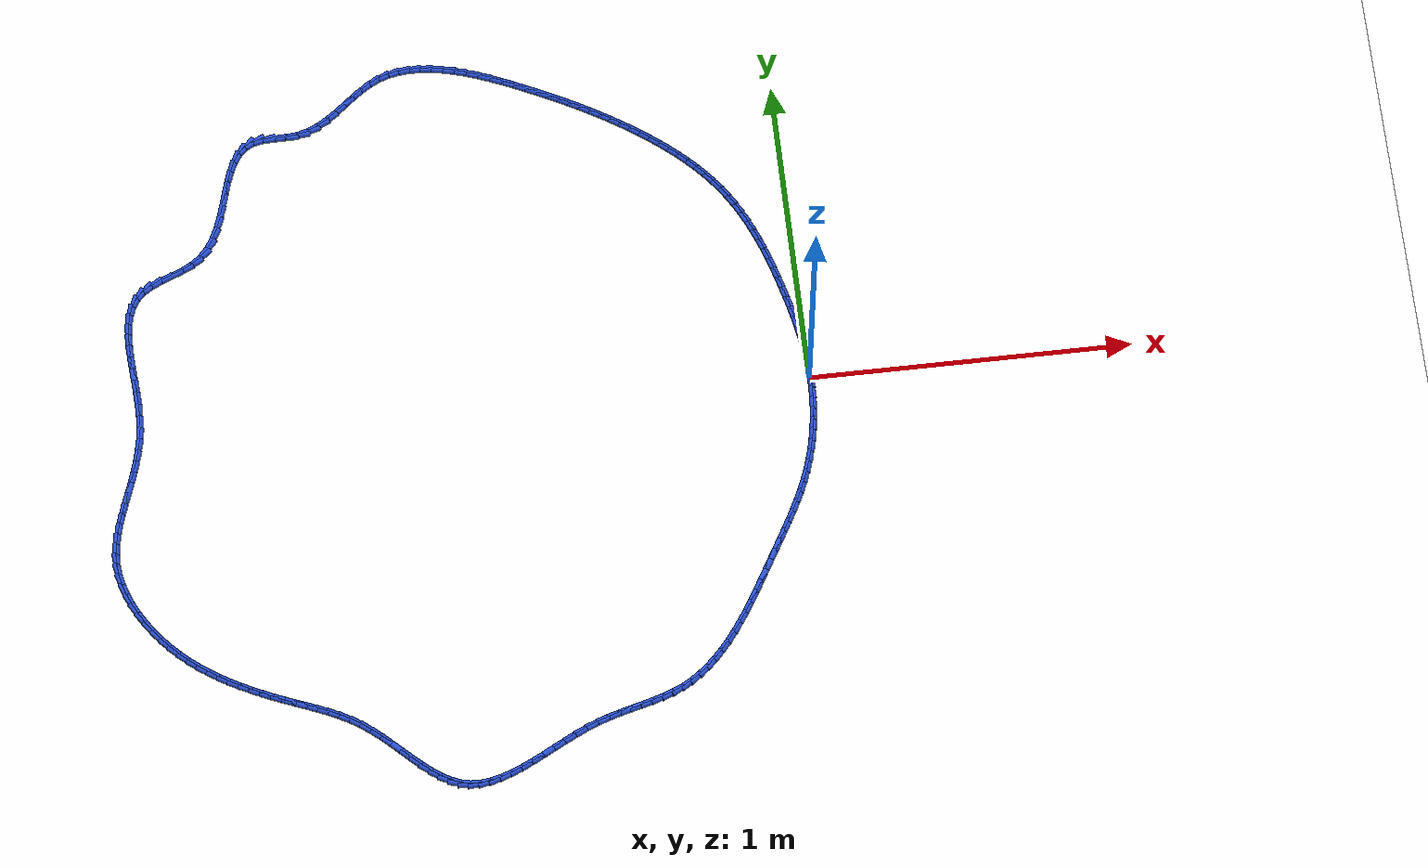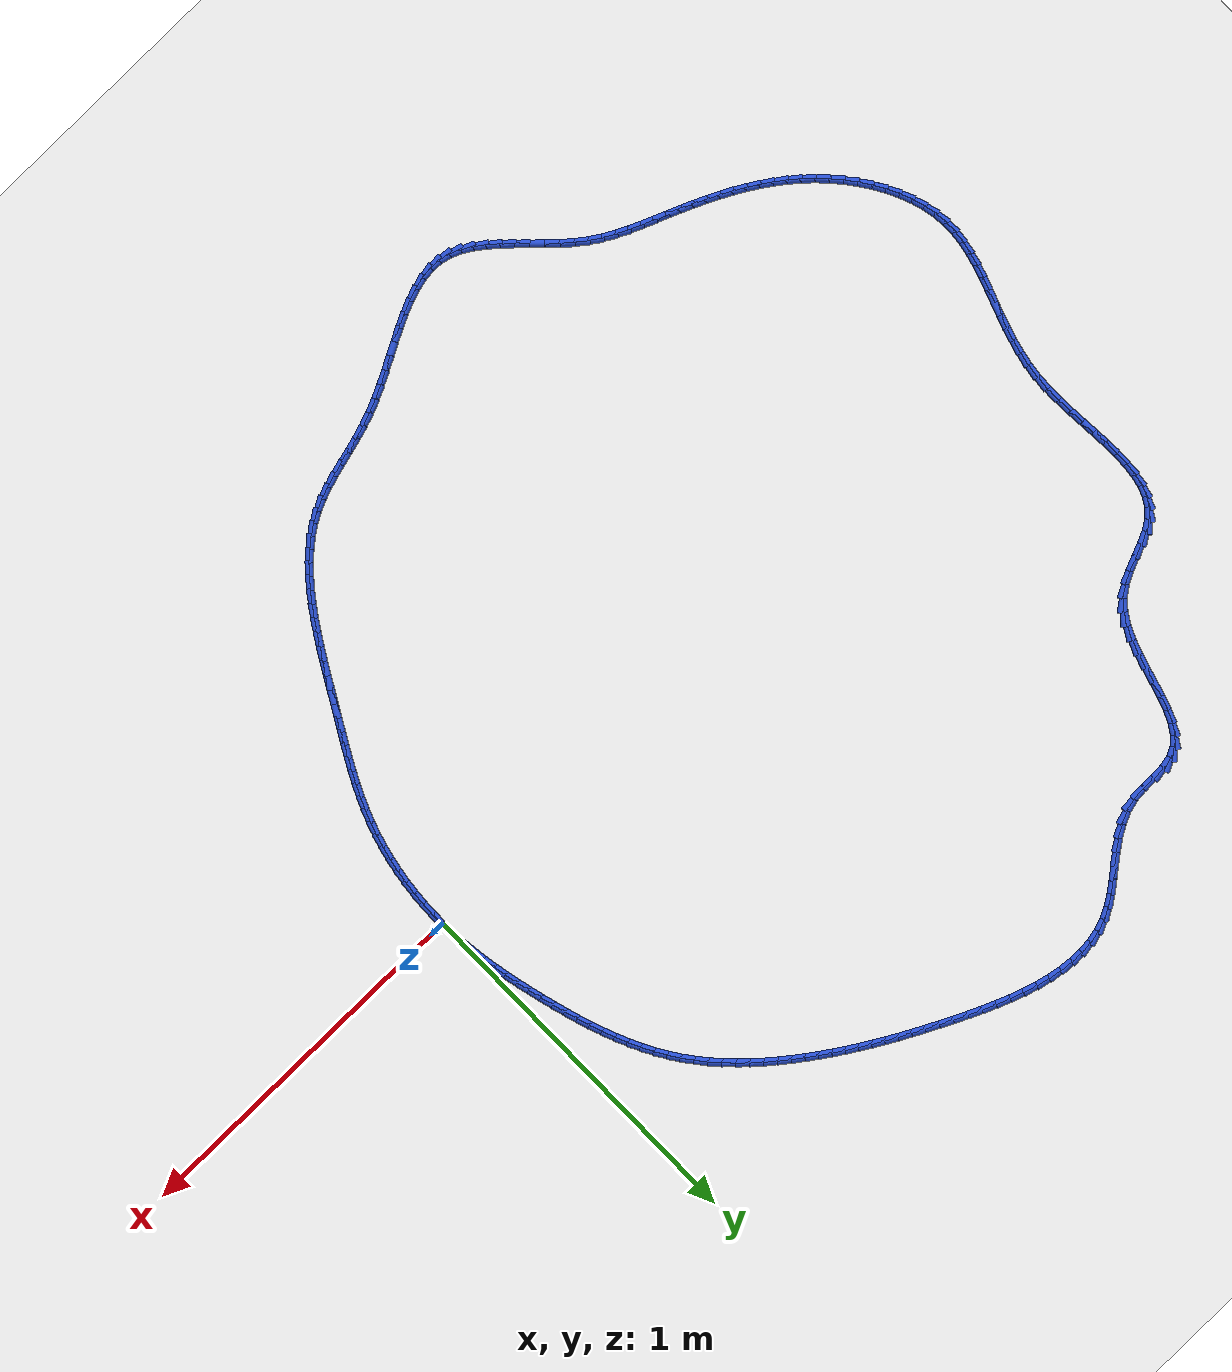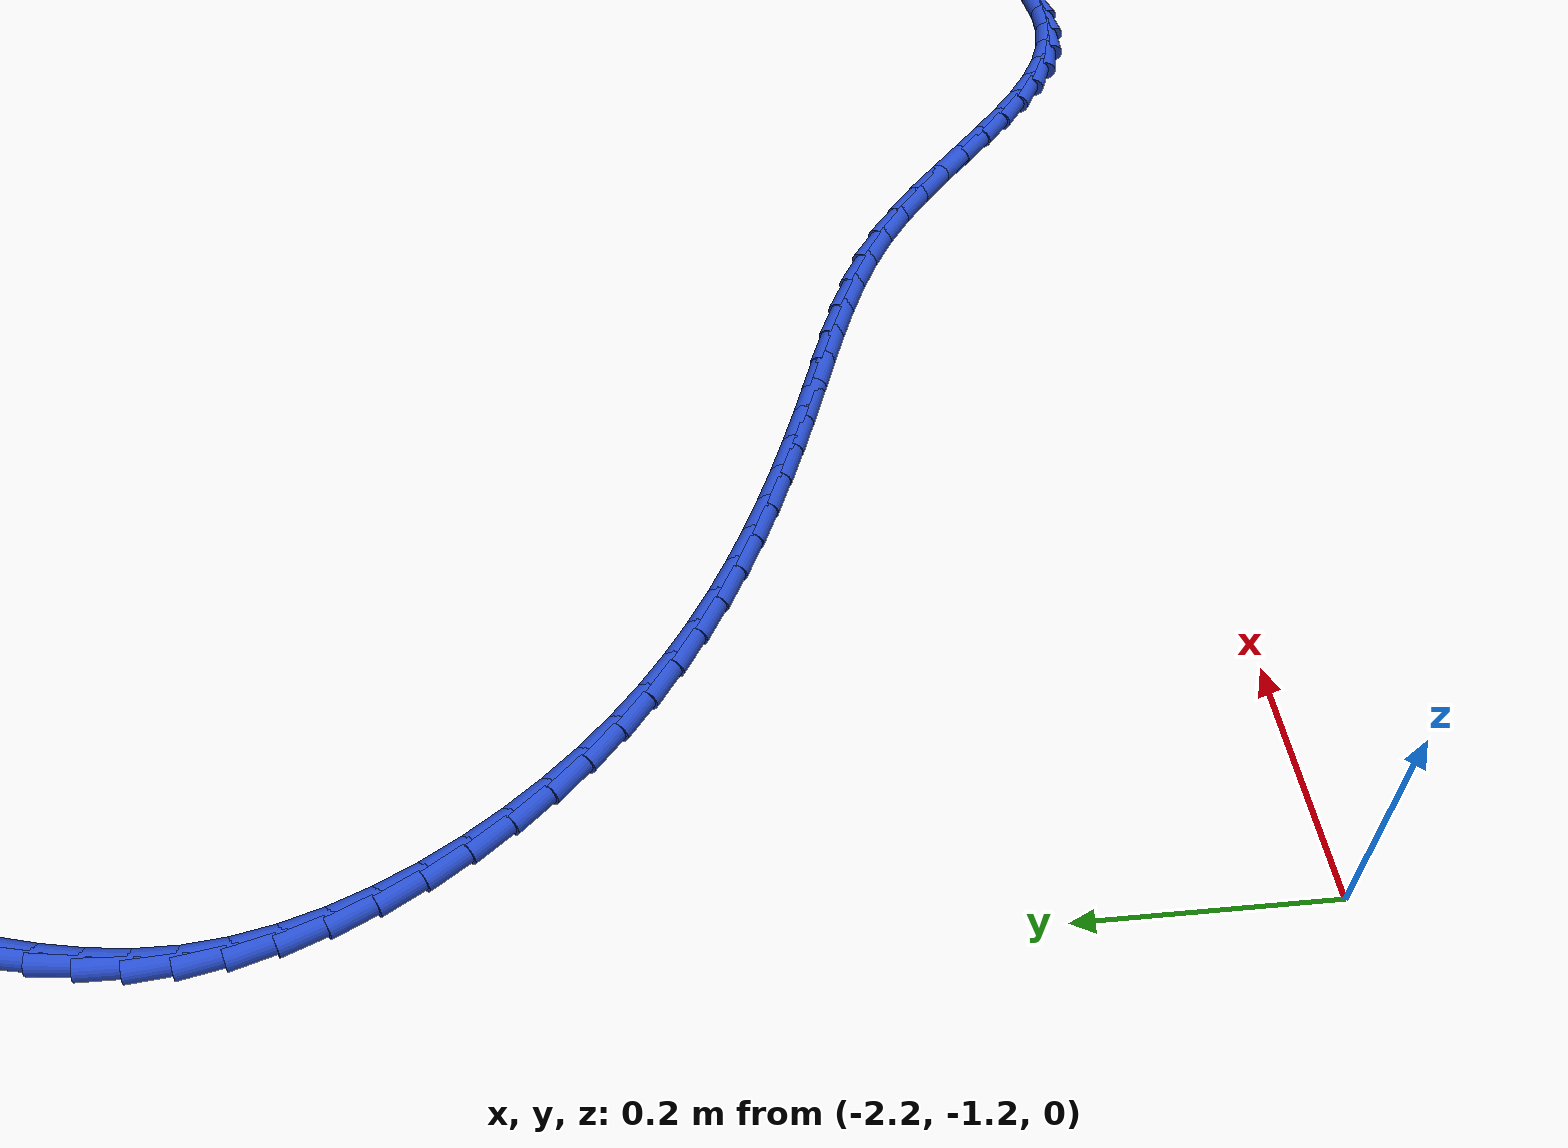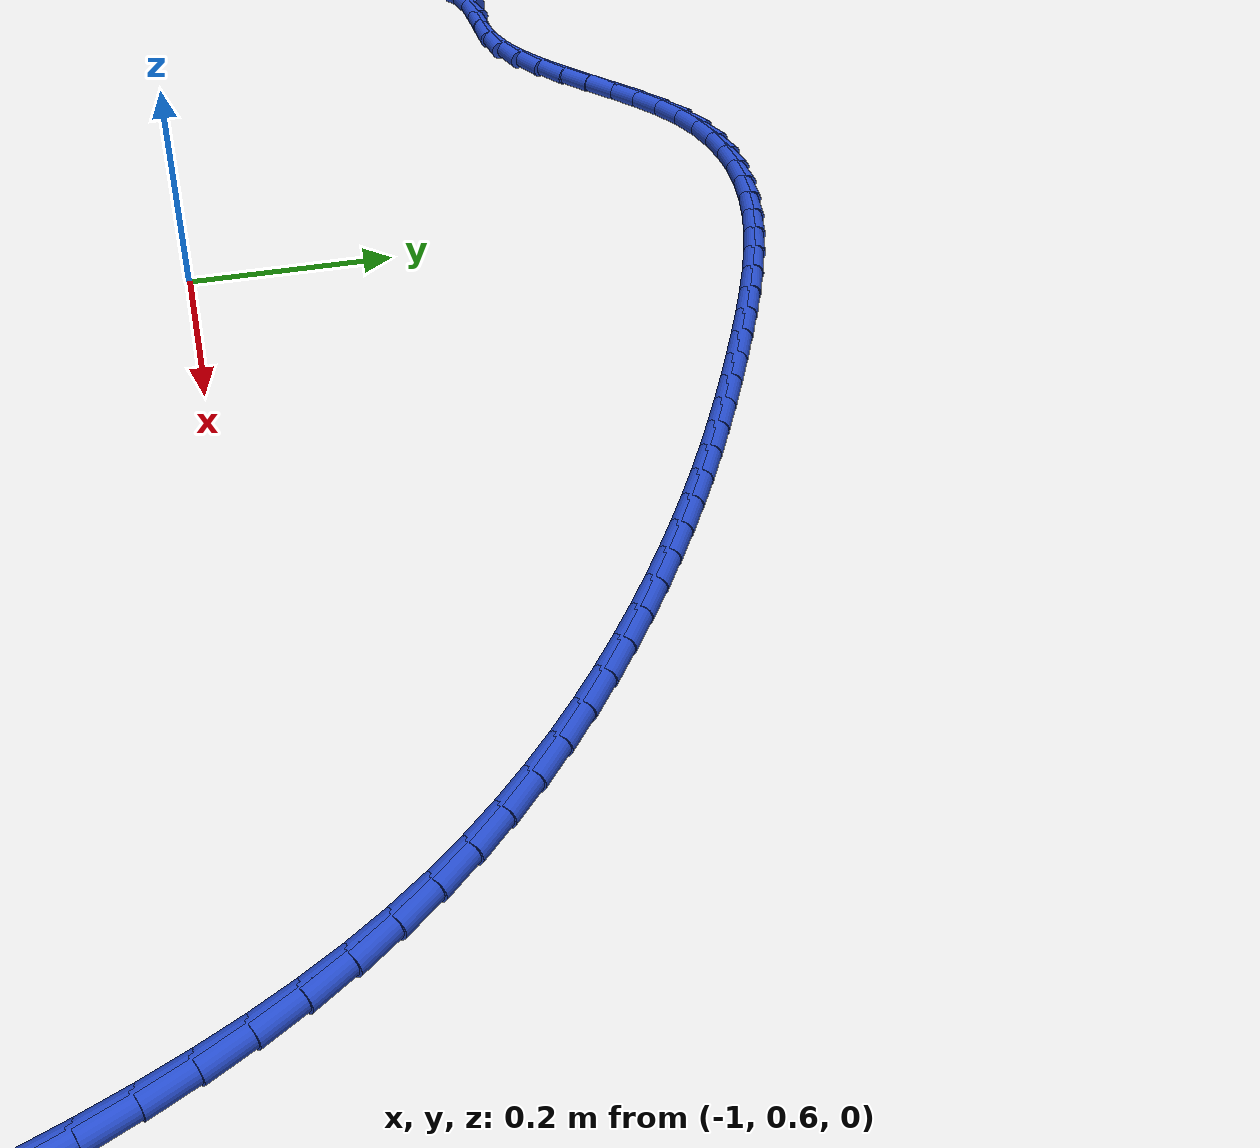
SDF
<sdf version="1.6">
 <world name="default">
  <light name="sun" type="directional">
   <pose>0 0 10 0 -0 0</pose>
   <diffuse>0.8 0.8 0.8 1</diffuse>
   <specular>0.2 0.2 0.2 1</specular>
   <attenuation>
    <range>1000</range>
    <constant>0.9</constant>
    <linear>0.01</linear>
    <quadratic>0.001</quadratic>
   </attenuation>
   <direction>-0.5 0.1 -0.9</direction>
  </light>
  <model name="ground_plane">
   <static>1</static>
   <link name="link">
    <collision name="collision">
     <geometry><plane><normal>0 0 1</normal><size>100 100</size></plane></geometry>
     <surface><friction><ode><mu>100</mu><mu2>50</mu2></ode></friction></surface>
    </collision>
    <visual name="visual">
     <cast_shadows>0</cast_shadows>
     <geometry><plane><normal>0 0 1</normal><size>100 100</size></plane></geometry>
     <material>
      <script><uri>file://media/materials/scripts/gazebo.material</uri><name>Gazebo/WhiteGlow</name></script>
     </material>
    </visual>
   </link>
  </model>
  <gravity>0 0 -9.8</gravity>
  <magnetic_field>6e-06 2.3e-05 -4.2e-05</magnetic_field>
  <atmosphere type="adiabatic"/>
  <physics name="default_physics" default="0" type="ode">
   <max_step_size>0.001</max_step_size>
   <real_time_factor>1</real_time_factor>
   <real_time_update_rate>1000</real_time_update_rate>
  </physics>
  <scene><ambient>0.4 0.4 0.4 1</ambient><background>0.7 0.7 0.7 1</background><shadows>1</shadows></scene>
  <spherical_coordinates>
   <surface_model>EARTH_WGS84</surface_model>
   <latitude_deg>0</latitude_deg>
   <longitude_deg>0</longitude_deg>
   <elevation>0</elevation>
   <heading_deg>0</heading_deg>
  </spherical_coordinates>
  <model name="line">
   <link name="link_0">
    <pose>1.734723475976807e-18 6.938893903907228e-18 0.01 0 1.57 -1.5310453082077948</pose>
    <collision name="collision">
     <geometry><cylinder><radius>0.01</radius><length>0.08</length></cylinder></geometry>
    </collision>
    <visual name="visual">
     <material>
      <script><name>Gazebo/Blue</name><uri>file://media/materials/scripts/gazebo.material</uri></script>
     </material>
     <geometry><cylinder><radius>0.01</radius><length>0.08</length></cylinder></geometry>
    </visual>
   </link>
   <link name="link_1">
    <pose>-0.0014066485565266734 0.03536783776255696 0.01 0 1.57 -1.4940458626089452</pose>
    <collision name="collision">
     <geometry><cylinder><radius>0.01</radius><length>0.08</length></cylinder></geometry>
    </collision>
    <visual name="visual">
     <material>
      <script><name>Gazebo/Blue</name><uri>file://media/materials/scripts/gazebo.material</uri></script>
     </material>
     <geometry><cylinder><radius>0.01</radius><length>0.08</length></cylinder></geometry>
    </visual>
   </link>
   <link name="link_2">
    <pose>-0.004113861491051096 0.07057146996437094 0.01 0 1.57 -1.4600752491633235</pose>
    <collision name="collision">
     <geometry><cylinder><radius>0.01</radius><length>0.08</length></cylinder></geometry>
    </collision>
    <visual name="visual">
     <material>
      <script><name>Gazebo/Blue</name><uri>file://media/materials/scripts/gazebo.material</uri></script>
     </material>
     <geometry><cylinder><radius>0.01</radius><length>0.08</length></cylinder></geometry>
    </visual>
   </link>
   <link name="link_3">
    <pose>-0.008011516258943882 0.10562996558287625 0.01 0 1.57 -1.4292463979921937</pose>
    <collision name="collision">
     <geometry><cylinder><radius>0.01</radius><length>0.08</length></cylinder></geometry>
    </collision>
    <visual name="visual">
     <material>
      <script><name>Gazebo/Blue</name><uri>file://media/materials/scripts/gazebo.material</uri></script>
     </material>
     <geometry><cylinder><radius>0.01</radius><length>0.08</length></cylinder></geometry>
    </visual>
   </link>
   <link name="link_4">
    <pose>-0.012989490315575633 0.14056239359550732 0.01 0 1.57 -1.4016290929852517</pose>
    <collision name="collision">
     <geometry><cylinder><radius>0.01</radius><length>0.08</length></cylinder></geometry>
    </collision>
    <visual name="visual">
     <material>
      <script><name>Gazebo/Blue</name><uri>file://media/materials/scripts/gazebo.material</uri></script>
     </material>
     <geometry><cylinder><radius>0.01</radius><length>0.08</length></cylinder></geometry>
    </visual>
   </link>
   <link name="link_5">
    <pose>-0.018937661116316947 0.1753878229796984 0.01 0 1.57 -1.3772583165151595</pose>
    <collision name="collision">
     <geometry><cylinder><radius>0.01</radius><length>0.08</length></cylinder></geometry>
    </collision>
    <visual name="visual">
     <material>
      <script><name>Gazebo/Blue</name><uri>file://media/materials/scripts/gazebo.material</uri></script>
     </material>
     <geometry><cylinder><radius>0.01</radius><length>0.08</length></cylinder></geometry>
    </visual>
   </link>
   <link name="link_6">
    <pose>-0.025745906116538438 0.21012532271288392 0.01 0 1.57 -1.356142556914128</pose>
    <collision name="collision">
     <geometry><cylinder><radius>0.01</radius><length>0.08</length></cylinder></geometry>
    </collision>
    <visual name="visual">
     <material>
      <script><name>Gazebo/Blue</name><uri>file://media/materials/scripts/gazebo.material</uri></script>
     </material>
     <geometry><cylinder><radius>0.01</radius><length>0.08</length></cylinder></geometry>
    </visual>
   </link>
   <link name="link_7">
    <pose>-0.03330410277161073 0.2447939617724983 0.01 0 1.57 -1.338271521490759</pose>
    <collision name="collision">
     <geometry><cylinder><radius>0.01</radius><length>0.08</length></cylinder></geometry>
    </collision>
    <visual name="visual">
     <material>
      <script><name>Gazebo/Blue</name><uri>file://media/materials/scripts/gazebo.material</uri></script>
     </material>
     <geometry><cylinder><radius>0.01</radius><length>0.08</length></cylinder></geometry>
    </visual>
   </link>
   <link name="link_8">
    <pose>-0.04150212853690438 0.27941280913597566 0.01 0 1.57 -1.323619609899118</pose>
    <collision name="collision">
     <geometry><cylinder><radius>0.01</radius><length>0.08</length></cylinder></geometry>
    </collision>
    <visual name="visual">
     <material>
      <script><name>Gazebo/Blue</name><uri>file://media/materials/scripts/gazebo.material</uri></script>
     </material>
     <geometry><cylinder><radius>0.01</radius><length>0.08</length></cylinder></geometry>
    </visual>
   </link>
   <link name="link_9">
    <pose>-0.05022996867380355 0.3140008791503931 0.01 0 1.57 -1.3105177332631843</pose>
    <collision name="collision">
     <geometry><cylinder><radius>0.01</radius><length>0.08</length></cylinder></geometry>
    </collision>
    <visual name="visual">
     <material>
      <script><name>Gazebo/Blue</name><uri>file://media/materials/scripts/gazebo.material</uri></script>
     </material>
     <geometry><cylinder><radius>0.01</radius><length>0.08</length></cylinder></geometry>
    </visual>
   </link>
   <link name="link_10">
    <pose>-0.05943110644077755 0.3485500762214679 0.01 0 1.57 -1.294639159193329</pose>
    <collision name="collision">
     <geometry><cylinder><radius>0.01</radius><length>0.08</length></cylinder></geometry>
    </collision>
    <visual name="visual">
     <material>
      <script><name>Gazebo/Blue</name><uri>file://media/materials/scripts/gazebo.material</uri></script>
     </material>
     <geometry><cylinder><radius>0.01</radius><length>0.08</length></cylinder></geometry>
    </visual>
   </link>
   <link name="link_11">
    <pose>-0.06918889312468006 0.3829814270724964 0.01 0 1.57 -1.275231451033211</pose>
    <collision name="collision">
     <geometry><cylinder><radius>0.01</radius><length>0.08</length></cylinder></geometry>
    </collision>
    <visual name="visual">
     <material>
      <script><name>Gazebo/Blue</name><uri>file://media/materials/scripts/gazebo.material</uri></script>
     </material>
     <geometry><cylinder><radius>0.01</radius><length>0.08</length></cylinder></geometry>
    </visual>
   </link>
   <link name="link_12">
    <pose>-0.07960925500252211 0.4172045186216846 0.01 0 1.57 -1.2522134530300866</pose>
    <collision name="collision">
     <geometry><cylinder><radius>0.01</radius><length>0.08</length></cylinder></geometry>
    </collision>
    <visual name="visual">
     <material>
      <script><name>Gazebo/Blue</name><uri>file://media/materials/scripts/gazebo.material</uri></script>
     </material>
     <geometry><cylinder><radius>0.01</radius><length>0.08</length></cylinder></geometry>
    </visual>
   </link>
   <link name="link_13">
    <pose>-0.0907981183513147 0.45112893778723906 0.01 0 1.57 -1.2254896771387778</pose>
    <collision name="collision">
     <geometry><cylinder><radius>0.01</radius><length>0.08</length></cylinder></geometry>
    </collision>
    <visual name="visual">
     <material>
      <script><name>Gazebo/Blue</name><uri>file://media/materials/scripts/gazebo.material</uri></script>
     </material>
     <geometry><cylinder><radius>0.01</radius><length>0.08</length></cylinder></geometry>
    </visual>
   </link>
   <link name="link_14">
    <pose>-0.10286140944806886 0.48466427148736574 0.01 0 1.57 -1.1949586788717386</pose>
    <collision name="collision">
     <geometry><cylinder><radius>0.01</radius><length>0.08</length></cylinder></geometry>
    </collision>
    <visual name="visual">
     <material>
      <script><name>Gazebo/Blue</name><uri>file://media/materials/scripts/gazebo.material</uri></script>
     </material>
     <geometry><cylinder><radius>0.01</radius><length>0.08</length></cylinder></geometry>
    </visual>
   </link>
   <link name="link_15">
    <pose>-0.11590505456979558 0.5177201066402711 0.01 0 1.57 -1.1605237380094044</pose>
    <collision name="collision">
     <geometry><cylinder><radius>0.01</radius><length>0.08</length></cylinder></geometry>
    </collision>
    <visual name="visual">
     <material>
      <script><name>Gazebo/Blue</name><uri>file://media/materials/scripts/gazebo.material</uri></script>
     </material>
     <geometry><cylinder><radius>0.01</radius><length>0.08</length></cylinder></geometry>
    </visual>
   </link>
   <link name="link_16">
    <pose>-0.13003497999350594 0.5502060301641614 0.01 0 1.57 -1.1221062574177487</pose>
    <collision name="collision">
     <geometry><cylinder><radius>0.01</radius><length>0.08</length></cylinder></geometry>
    </collision>
    <visual name="visual">
     <material>
      <script><name>Gazebo/Blue</name><uri>file://media/materials/scripts/gazebo.material</uri></script>
     </material>
     <geometry><cylinder><radius>0.01</radius><length>0.08</length></cylinder></geometry>
    </visual>
   </link>
   <link name="link_17">
    <pose>-0.14535711199621087 0.5820316289772426 0.01 0 1.57 -1.0796620651295834</pose>
    <collision name="collision">
     <geometry><cylinder><radius>0.01</radius><length>0.08</length></cylinder></geometry>
    </collision>
    <visual name="visual">
     <material>
      <script><name>Gazebo/Blue</name><uri>file://media/materials/scripts/gazebo.material</uri></script>
     </material>
     <geometry><cylinder><radius>0.01</radius><length>0.08</length></cylinder></geometry>
    </visual>
   </link>
   <link name="link_18">
    <pose>-0.16197737685492147 0.6131064899977213 0.01 0 1.57 -1.0332003728123056</pose>
    <collision name="collision">
     <geometry><cylinder><radius>0.01</radius><length>0.08</length></cylinder></geometry>
    </collision>
    <visual name="visual">
     <material>
      <script><name>Gazebo/Blue</name><uri>file://media/materials/scripts/gazebo.material</uri></script>
     </material>
     <geometry><cylinder><radius>0.01</radius><length>0.08</length></cylinder></geometry>
    </visual>
   </link>
   <link name="link_19">
    <pose>-0.18000170084664874 0.6433402001438037 0.01 0 1.57 -0.9828084889556159</pose>
    <collision name="collision">
     <geometry><cylinder><radius>0.01</radius><length>0.08</length></cylinder></geometry>
    </collision>
    <visual name="visual">
     <material>
      <script><name>Gazebo/Blue</name><uri>file://media/materials/scripts/gazebo.material</uri></script>
     </material>
     <geometry><cylinder><radius>0.01</radius><length>0.08</length></cylinder></geometry>
    </visual>
   </link>
   <link name="link_20">
    <pose>-0.19953587932387218 0.6726424052973401 0.01 0 1.57 -0.9305583617726472</pose>
    <collision name="collision">
     <geometry><cylinder><radius>0.01</radius><length>0.08</length></cylinder></geometry>
    </collision>
    <visual name="visual">
     <material>
      <script><name>Gazebo/Blue</name><uri>file://media/materials/scripts/gazebo.material</uri></script>
     </material>
     <geometry><cylinder><radius>0.01</radius><length>0.08</length></cylinder></geometry>
    </visual>
   </link>
   <link name="link_21">
    <pose>-0.22062325139379949 0.700950879359868 0.01 0 1.57 -0.8814752981085816</pose>
    <collision name="collision">
     <geometry><cylinder><radius>0.01</radius><length>0.08</length></cylinder></geometry>
    </collision>
    <visual name="visual">
     <material>
      <script><name>Gazebo/Blue</name><uri>file://media/materials/scripts/gazebo.material</uri></script>
     </material>
     <geometry><cylinder><radius>0.01</radius><length>0.08</length></cylinder></geometry>
    </visual>
   </link>
   <link name="link_22">
    <pose>-0.24314488133618367 0.7282764789089937 0.01 0 1.57 -0.836262044691703</pose>
    <collision name="collision">
     <geometry><cylinder><radius>0.01</radius><length>0.08</length></cylinder></geometry>
    </collision>
    <visual name="visual">
     <material>
      <script><name>Gazebo/Blue</name><uri>file://media/materials/scripts/gazebo.material</uri></script>
     </material>
     <geometry><cylinder><radius>0.01</radius><length>0.08</length></cylinder></geometry>
    </visual>
   </link>
   <link name="link_23">
    <pose>-0.266955818069513 0.7546417768941707 0.01 0 1.57 -0.7947716503147767</pose>
    <collision name="collision">
     <geometry><cylinder><radius>0.01</radius><length>0.08</length></cylinder></geometry>
    </collision>
    <visual name="visual">
     <material>
      <script><name>Gazebo/Blue</name><uri>file://media/materials/scripts/gazebo.material</uri></script>
     </material>
     <geometry><cylinder><radius>0.01</radius><length>0.08</length></cylinder></geometry>
    </visual>
   </link>
   <link name="link_24">
    <pose>-0.29191111051227586 0.7800693462648527 0.01 0 1.57 -0.7568272609245303</pose>
    <collision name="collision">
     <geometry><cylinder><radius>0.01</radius><length>0.08</length></cylinder></geometry>
    </collision>
    <visual name="visual">
     <material>
      <script><name>Gazebo/Blue</name><uri>file://media/materials/scripts/gazebo.material</uri></script>
     </material>
     <geometry><cylinder><radius>0.01</radius><length>0.08</length></cylinder></geometry>
    </visual>
   </link>
   <link name="link_25">
    <pose>-0.31786580758296057 0.8045817599704931 0.01 0 1.57 -0.7222384978069104</pose>
    <collision name="collision">
     <geometry><cylinder><radius>0.01</radius><length>0.08</length></cylinder></geometry>
    </collision>
    <visual name="visual">
     <material>
      <script><name>Gazebo/Blue</name><uri>file://media/materials/scripts/gazebo.material</uri></script>
     </material>
     <geometry><cylinder><radius>0.01</radius><length>0.08</length></cylinder></geometry>
    </visual>
   </link>
   <link name="link_26">
    <pose>-0.34467495820005556 0.8282015909605458 0.01 0 1.57 -0.6908139829027834</pose>
    <collision name="collision">
     <geometry><cylinder><radius>0.01</radius><length>0.08</length></cylinder></geometry>
    </collision>
    <visual name="visual">
     <material>
      <script><name>Gazebo/Blue</name><uri>file://media/materials/scripts/gazebo.material</uri></script>
     </material>
     <geometry><cylinder><radius>0.01</radius><length>0.08</length></cylinder></geometry>
    </visual>
   </link>
   <link name="link_27">
    <pose>-0.3721936112820491 0.8509514121844646 0.01 0 1.57 -0.6623706099893018</pose>
    <collision name="collision">
     <geometry><cylinder><radius>0.01</radius><length>0.08</length></cylinder></geometry>
    </collision>
    <visual name="visual">
     <material>
      <script><name>Gazebo/Blue</name><uri>file://media/materials/scripts/gazebo.material</uri></script>
     </material>
     <geometry><cylinder><radius>0.01</radius><length>0.08</length></cylinder></geometry>
    </visual>
   </link>
   <link name="link_28">
    <pose>-0.4002768157474295 0.8728537965917029 0.01 0 1.57 -0.6367402854858322</pose>
    <collision name="collision">
     <geometry><cylinder><radius>0.01</radius><length>0.08</length></cylinder></geometry>
    </collision>
    <visual name="visual">
     <material>
      <script><name>Gazebo/Blue</name><uri>file://media/materials/scripts/gazebo.material</uri></script>
     </material>
     <geometry><cylinder><radius>0.01</radius><length>0.08</length></cylinder></geometry>
    </visual>
   </link>
   <link name="link_29">
    <pose>-0.4287796205146852 0.8939313171317147 0.01 0 1.57 -0.6137748607162741</pose>
    <collision name="collision">
     <geometry><cylinder><radius>0.01</radius><length>0.08</length></cylinder></geometry>
    </collision>
    <visual name="visual">
     <material>
      <script><name>Gazebo/Blue</name><uri>file://media/materials/scripts/gazebo.material</uri></script>
     </material>
     <geometry><cylinder><radius>0.01</radius><length>0.08</length></cylinder></geometry>
    </visual>
   </link>
   <link name="link_30">
    <pose>-0.4575570745023046 0.9142065467539535 0.01 0 1.57 -0.5930610244994271</pose>
    <collision name="collision">
     <geometry><cylinder><radius>0.01</radius><length>0.08</length></cylinder></geometry>
    </collision>
    <visual name="visual">
     <material>
      <script><name>Gazebo/Blue</name><uri>file://media/materials/scripts/gazebo.material</uri></script>
     </material>
     <geometry><cylinder><radius>0.01</radius><length>0.08</length></cylinder></geometry>
    </visual>
   </link>
   <link name="link_31">
    <pose>-0.48649570820087723 0.9337111297477674 0.01 0 1.57 -0.573235141384124</pose>
    <collision name="collision">
     <geometry><cylinder><radius>0.01</radius><length>0.08</length></cylinder></geometry>
    </collision>
    <visual name="visual">
     <material>
      <script><name>Gazebo/Blue</name><uri>file://media/materials/scripts/gazebo.material</uri></script>
     </material>
     <geometry><cylinder><radius>0.01</radius><length>0.08</length></cylinder></geometry>
    </visual>
   </link>
   <link name="link_32">
    <pose>-0.515632219225156 0.9525199807010726 0.01 0 1.57 -0.5540895461940869</pose>
    <collision name="collision">
     <geometry><cylinder><radius>0.01</radius><length>0.08</length></cylinder></geometry>
    </collision>
    <visual name="visual">
     <material>
      <script><name>Gazebo/Blue</name><uri>file://media/materials/scripts/gazebo.material</uri></script>
     </material>
     <geometry><cylinder><radius>0.01</radius><length>0.08</length></cylinder></geometry>
    </visual>
   </link>
   <link name="link_33">
    <pose>-0.5450480302908421 0.9707209016329209 0.01 0 1.57 -0.5358354134404212</pose>
    <collision name="collision">
     <geometry><cylinder><radius>0.01</radius><length>0.08</length></cylinder></geometry>
    </collision>
    <visual name="visual">
     <material>
      <script><name>Gazebo/Blue</name><uri>file://media/materials/scripts/gazebo.material</uri></script>
     </material>
     <geometry><cylinder><radius>0.01</radius><length>0.08</length></cylinder></geometry>
    </visual>
   </link>
   <link name="link_34">
    <pose>-0.5748245716936354 0.9884016967465236 0.01 0 1.57 -0.5186631136779175</pose>
    <collision name="collision">
     <geometry><cylinder><radius>0.01</radius><length>0.08</length></cylinder></geometry>
    </collision>
    <visual name="visual">
     <material>
      <script><name>Gazebo/Blue</name><uri>file://media/materials/scripts/gazebo.material</uri></script>
     </material>
     <geometry><cylinder><radius>0.01</radius><length>0.08</length></cylinder></geometry>
    </visual>
   </link>
   <link name="link_35">
    <pose>-0.605043273729235 1.005650170245091 0.01 0 1.57 -0.5027356909325598</pose>
    <collision name="collision">
     <geometry><cylinder><radius>0.01</radius><length>0.08</length></cylinder></geometry>
    </collision>
    <visual name="visual">
     <material>
      <script><name>Gazebo/Blue</name><uri>file://media/materials/scripts/gazebo.material</uri></script>
     </material>
     <geometry><cylinder><radius>0.01</radius><length>0.08</length></cylinder></geometry>
    </visual>
   </link>
   <link name="link_36">
    <pose>-0.6357855666933411 1.0225541263318343 0.01 0 1.57 -0.4881842220097204</pose>
    <collision name="collision">
     <geometry><cylinder><radius>0.01</radius><length>0.08</length></cylinder></geometry>
    </collision>
    <visual name="visual">
     <material>
      <script><name>Gazebo/Blue</name><uri>file://media/materials/scripts/gazebo.material</uri></script>
     </material>
     <geometry><cylinder><radius>0.01</radius><length>0.08</length></cylinder></geometry>
    </visual>
   </link>
   <link name="link_37">
    <pose>-0.6671328808816522 1.039201369209963 0.01 0 1.57 -0.47510520087693137</pose>
    <collision name="collision">
     <geometry><cylinder><radius>0.01</radius><length>0.08</length></cylinder></geometry>
    </collision>
    <visual name="visual">
     <material>
      <script><name>Gazebo/Blue</name><uri>file://media/materials/scripts/gazebo.material</uri></script>
     </material>
     <geometry><cylinder><radius>0.01</radius><length>0.08</length></cylinder></geometry>
    </visual>
   </link>
   <link name="link_38">
    <pose>-0.6991666465898684 1.0556797030826888 0.01 0 1.57 -0.46355993416197067</pose>
    <collision name="collision">
     <geometry><cylinder><radius>0.01</radius><length>0.08</length></cylinder></geometry>
    </collision>
    <visual name="visual">
     <material>
      <script><name>Gazebo/Blue</name><uri>file://media/materials/scripts/gazebo.material</uri></script>
     </material>
     <geometry><cylinder><radius>0.01</radius><length>0.08</length></cylinder></geometry>
    </visual>
   </link>
   <link name="link_39">
    <pose>-0.7319682941136888 1.0720769321532215 0.01 0 1.57 -0.4535450218004484</pose>
    <collision name="collision">
     <geometry><cylinder><radius>0.01</radius><length>0.08</length></cylinder></geometry>
    </collision>
    <visual name="visual">
     <material>
      <script><name>Gazebo/Blue</name><uri>file://media/materials/scripts/gazebo.material</uri></script>
     </material>
     <geometry><cylinder><radius>0.01</radius><length>0.08</length></cylinder></geometry>
    </visual>
   </link>
   <link name="link_40">
    <pose>-0.7656182217290372 1.0884790781928786 0.01 0 1.57 -0.44251287198266465</pose>
    <collision name="collision">
     <geometry><cylinder><radius>0.01</radius><length>0.08</length></cylinder></geometry>
    </collision>
    <visual name="visual">
     <material>
      <script><name>Gazebo/Blue</name><uri>file://media/materials/scripts/gazebo.material</uri></script>
     </material>
     <geometry><cylinder><radius>0.01</radius><length>0.08</length></cylinder></geometry>
    </visual>
   </link>
   <link name="link_41">
    <pose>-0.8001107535066229 1.1048235016660994 0.01 0 1.57 -0.42603625308372434</pose>
    <collision name="collision">
     <geometry><cylinder><radius>0.01</radius><length>0.08</length></cylinder></geometry>
    </collision>
    <visual name="visual">
     <material>
      <script><name>Gazebo/Blue</name><uri>file://media/materials/scripts/gazebo.material</uri></script>
     </material>
     <geometry><cylinder><radius>0.01</radius><length>0.08</length></cylinder></geometry>
    </visual>
   </link>
   <link name="link_42">
    <pose>-0.8352906702248071 1.120789282391924 0.01 0 1.57 -0.40350936769608253</pose>
    <collision name="collision">
     <geometry><cylinder><radius>0.01</radius><length>0.08</length></cylinder></geometry>
    </collision>
    <visual name="visual">
     <material>
      <script><name>Gazebo/Blue</name><uri>file://media/materials/scripts/gazebo.material</uri></script>
     </material>
     <geometry><cylinder><radius>0.01</radius><length>0.08</length></cylinder></geometry>
    </visual>
   </link>
   <link name="link_43">
    <pose>-0.8709877995981985 1.1360296743105016 0.01 0 1.57 -0.3745270180034008</pose>
    <collision name="collision">
     <geometry><cylinder><radius>0.01</radius><length>0.08</length></cylinder></geometry>
    </collision>
    <visual name="visual">
     <material>
      <script><name>Gazebo/Blue</name><uri>file://media/materials/scripts/gazebo.material</uri></script>
     </material>
     <geometry><cylinder><radius>0.01</radius><length>0.08</length></cylinder></geometry>
    </visual>
   </link>
   <link name="link_44">
    <pose>-0.9070319693414046 1.150197931361981 0.01 0 1.57 -0.33844490134135236</pose>
    <collision name="collision">
     <geometry><cylinder><radius>0.01</radius><length>0.08</length></cylinder></geometry>
    </collision>
    <visual name="visual">
     <material>
      <script><name>Gazebo/Blue</name><uri>file://media/materials/scripts/gazebo.material</uri></script>
     </material>
     <geometry><cylinder><radius>0.01</radius><length>0.08</length></cylinder></geometry>
    </visual>
   </link>
   <link name="link_45">
    <pose>-0.9432530071690333 1.1629473074865113 0.01 0 1.57 -0.2943773504879512</pose>
    <collision name="collision">
     <geometry><cylinder><radius>0.01</radius><length>0.08</length></cylinder></geometry>
    </collision>
    <visual name="visual">
     <material>
      <script><name>Gazebo/Blue</name><uri>file://media/materials/scripts/gazebo.material</uri></script>
     </material>
     <geometry><cylinder><radius>0.01</radius><length>0.08</length></cylinder></geometry>
    </visual>
   </link>
   <link name="link_46">
    <pose>-0.979480740795692 1.1739310566242411 0.01 0 1.57 -0.2411991551934628</pose>
    <collision name="collision">
     <geometry><cylinder><radius>0.01</radius><length>0.08</length></cylinder></geometry>
    </collision>
    <visual name="visual">
     <material>
      <script><name>Gazebo/Blue</name><uri>file://media/materials/scripts/gazebo.material</uri></script>
     </material>
     <geometry><cylinder><radius>0.01</radius><length>0.08</length></cylinder></geometry>
    </visual>
   </link>
   <link name="link_47">
    <pose>-1.0155449979359892 1.1828024327153202 0.01 0 1.57 -0.177570974918984</pose>
    <collision name="collision">
     <geometry><cylinder><radius>0.01</radius><length>0.08</length></cylinder></geometry>
    </collision>
    <visual name="visual">
     <material>
      <script><name>Gazebo/Blue</name><uri>file://media/materials/scripts/gazebo.material</uri></script>
     </material>
     <geometry><cylinder><radius>0.01</radius><length>0.08</length></cylinder></geometry>
    </visual>
   </link>
   <link name="link_48">
    <pose>-1.0512756063045319 1.189214689699897 0.01 0 1.57 -0.10202097017545224</pose>
    <collision name="collision">
     <geometry><cylinder><radius>0.01</radius><length>0.08</length></cylinder></geometry>
    </collision>
    <visual name="visual">
     <material>
      <script><name>Gazebo/Blue</name><uri>file://media/materials/scripts/gazebo.material</uri></script>
     </material>
     <geometry><cylinder><radius>0.01</radius><length>0.08</length></cylinder></geometry>
    </visual>
   </link>
   <link name="link_49">
    <pose>-1.0865023936159288 1.192821081518121 0.01 0 1.57 -0.013132208832821199</pose>
    <collision name="collision">
     <geometry><cylinder><radius>0.01</radius><length>0.08</length></cylinder></geometry>
    </collision>
    <visual name="visual">
     <material>
      <script><name>Gazebo/Blue</name><uri>file://media/materials/scripts/gazebo.material</uri></script>
     </material>
     <geometry><cylinder><radius>0.01</radius><length>0.08</length></cylinder></geometry>
    </visual>
   </link>
   <link name="link_50">
    <pose>-1.1210551875847874 1.193274862110141 0.01 0 1.57 0.09010541359045988</pose>
    <collision name="collision">
     <geometry><cylinder><radius>0.01</radius><length>0.08</length></cylinder></geometry>
    </collision>
    <visual name="visual">
     <material>
      <script><name>Gazebo/Blue</name><uri>file://media/materials/scripts/gazebo.material</uri></script>
     </material>
     <geometry><cylinder><radius>0.01</radius><length>0.08</length></cylinder></geometry>
    </visual>
   </link>
   <link name="link_51">
    <pose>-1.1547638159257152 1.1902292854161058 0.01 0 1.57 0.20775018705595957</pose>
    <collision name="collision">
     <geometry><cylinder><radius>0.01</radius><length>0.08</length></cylinder></geometry>
    </collision>
    <visual name="visual">
     <material>
      <script><name>Gazebo/Blue</name><uri>file://media/materials/scripts/gazebo.material</uri></script>
     </material>
     <geometry><cylinder><radius>0.01</radius><length>0.08</length></cylinder></geometry>
    </visual>
   </link>
   <link name="link_52">
    <pose>-1.1874581063533205 1.1833376053761648 0.01 0 1.57 0.3382602199083529</pose>
    <collision name="collision">
     <geometry><cylinder><radius>0.01</radius><length>0.08</length></cylinder></geometry>
    </collision>
    <visual name="visual">
     <material>
      <script><name>Gazebo/Blue</name><uri>file://media/materials/scripts/gazebo.material</uri></script>
     </material>
     <geometry><cylinder><radius>0.01</radius><length>0.08</length></cylinder></geometry>
    </visual>
   </link>
   <link name="link_53">
    <pose>-1.2189678865822107 1.1722530759304666 0.01 0 1.57 0.4747191054613439</pose>
    <collision name="collision">
     <geometry><cylinder><radius>0.01</radius><length>0.08</length></cylinder></geometry>
    </collision>
    <visual name="visual">
     <material>
      <script><name>Gazebo/Blue</name><uri>file://media/materials/scripts/gazebo.material</uri></script>
     </material>
     <geometry><cylinder><radius>0.01</radius><length>0.08</length></cylinder></geometry>
    </visual>
   </link>
   <link name="link_54">
    <pose>-1.2491635338609743 1.1567350200682844 0.01 0 1.57 0.5830899793063574</pose>
    <collision name="collision">
     <geometry><cylinder><radius>0.01</radius><length>0.08</length></cylinder></geometry>
    </collision>
    <visual name="visual">
     <material>
      <script><name>Gazebo/Blue</name><uri>file://media/materials/scripts/gazebo.material</uri></script>
     </material>
     <geometry><cylinder><radius>0.01</radius><length>0.08</length></cylinder></geometry>
    </visual>
   </link>
   <link name="link_55">
    <pose>-1.2782902490373502 1.1375232204500374 0.01 0 1.57 0.649231325469338</pose>
    <collision name="collision">
     <geometry><cylinder><radius>0.01</radius><length>0.08</length></cylinder></geometry>
    </collision>
    <visual name="visual">
     <material>
      <script><name>Gazebo/Blue</name><uri>file://media/materials/scripts/gazebo.material</uri></script>
     </material>
     <geometry><cylinder><radius>0.01</radius><length>0.08</length></cylinder></geometry>
    </visual>
   </link>
   <link name="link_56">
    <pose>-1.306795917609366 1.1158876401357187 0.01 0 1.57 0.6772452412578903</pose>
    <collision name="collision">
     <geometry><cylinder><radius>0.01</radius><length>0.08</length></cylinder></geometry>
    </collision>
    <visual name="visual">
     <material>
      <script><name>Gazebo/Blue</name><uri>file://media/materials/scripts/gazebo.material</uri></script>
     </material>
     <geometry><cylinder><radius>0.01</radius><length>0.08</length></cylinder></geometry>
    </visual>
   </link>
   <link name="link_57">
    <pose>-1.3351304120024547 1.093103439569356 0.01 0 1.57 0.6697581610197426</pose>
    <collision name="collision">
     <geometry><cylinder><radius>0.01</radius><length>0.08</length></cylinder></geometry>
    </collision>
    <visual name="visual">
     <material>
      <script><name>Gazebo/Blue</name><uri>file://media/materials/scripts/gazebo.material</uri></script>
     </material>
     <geometry><cylinder><radius>0.01</radius><length>0.08</length></cylinder></geometry>
    </visual>
   </link>
   <link name="link_58">
    <pose>-1.3637436046420477 1.070445779194976 0.01 0 1.57 0.6269323758624077</pose>
    <collision name="collision">
     <geometry><cylinder><radius>0.01</radius><length>0.08</length></cylinder></geometry>
    </collision>
    <visual name="visual">
     <material>
      <script><name>Gazebo/Blue</name><uri>file://media/materials/scripts/gazebo.material</uri></script>
     </material>
     <geometry><cylinder><radius>0.01</radius><length>0.08</length></cylinder></geometry>
    </visual>
   </link>
   <link name="link_59">
    <pose>-1.3930853679535784 1.049189819456607 0.01 0 1.57 0.5468266544958442</pose>
    <collision name="collision">
     <geometry><cylinder><radius>0.01</radius><length>0.08</length></cylinder></geometry>
    </collision>
    <visual name="visual">
     <material>
      <script><name>Gazebo/Blue</name><uri>file://media/materials/scripts/gazebo.material</uri></script>
     </material>
     <geometry><cylinder><radius>0.01</radius><length>0.08</length></cylinder></geometry>
    </visual>
   </link>
   <link name="link_60">
    <pose>-1.4236055743624791 1.0306107207982758 0.01 0 1.57 0.42699124673926014</pose>
    <collision name="collision">
     <geometry><cylinder><radius>0.01</radius><length>0.08</length></cylinder></geometry>
    </collision>
    <visual name="visual">
     <material>
      <script><name>Gazebo/Blue</name><uri>file://media/materials/scripts/gazebo.material</uri></script>
     </material>
     <geometry><cylinder><radius>0.01</radius><length>0.08</length></cylinder></geometry>
    </visual>
   </link>
   <link name="link_61">
    <pose>-1.4557540962941813 1.0159836436640095 0.01 0 1.57 0.26802800167505036</pose>
    <collision name="collision">
     <geometry><cylinder><radius>0.01</radius><length>0.08</length></cylinder></geometry>
    </collision>
    <visual name="visual">
     <material>
      <script><name>Gazebo/Blue</name><uri>file://media/materials/scripts/gazebo.material</uri></script>
     </material>
     <geometry><cylinder><radius>0.01</radius><length>0.08</length></cylinder></geometry>
    </visual>
   </link>
   <link name="link_62">
    <pose>-1.4899808061741184 1.0065837484978362 0.01 0 1.57 0.09668751005792002</pose>
    <collision name="collision">
     <geometry><cylinder><radius>0.01</radius><length>0.08</length></cylinder></geometry>
    </collision>
    <visual name="visual">
     <material>
      <script><name>Gazebo/Blue</name><uri>file://media/materials/scripts/gazebo.material</uri></script>
     </material>
     <geometry><cylinder><radius>0.01</radius><length>0.08</length></cylinder></geometry>
    </visual>
   </link>
   <link name="link_63">
    <pose>-1.5264119443233584 1.0030502947924755 0.01 0 1.57 0.012838932992825793</pose>
    <collision name="collision">
     <geometry><cylinder><radius>0.01</radius><length>0.08</length></cylinder></geometry>
    </collision>
    <visual name="visual">
     <material>
      <script><name>Gazebo/Blue</name><uri>file://media/materials/scripts/gazebo.material</uri></script>
     </material>
     <geometry><cylinder><radius>0.01</radius><length>0.08</length></cylinder></geometry>
    </visual>
   </link>
   <link name="link_64">
    <pose>-1.5634192454608966 1.0025751344244451 0.01 0 1.57 0.039223806656412355</pose>
    <collision name="collision">
     <geometry><cylinder><radius>0.01</radius><length>0.08</length></cylinder></geometry>
    </collision>
    <visual name="visual">
     <material>
      <script><name>Gazebo/Blue</name><uri>file://media/materials/scripts/gazebo.material</uri></script>
     </material>
     <geometry><cylinder><radius>0.01</radius><length>0.08</length></cylinder></geometry>
    </visual>
   </link>
   <link name="link_65">
    <pose>-1.5987826628546415 1.00118733479172 0.01 0 1.57 0.1965188772060571</pose>
    <collision name="collision">
     <geometry><cylinder><radius>0.01</radius><length>0.08</length></cylinder></geometry>
    </collision>
    <visual name="visual">
     <material>
      <script><name>Gazebo/Blue</name><uri>file://media/materials/scripts/gazebo.material</uri></script>
     </material>
     <geometry><cylinder><radius>0.01</radius><length>0.08</length></cylinder></geometry>
    </visual>
   </link>
   <link name="link_66">
    <pose>-1.6302823328229852 0.9949161155931605 0.01 0 1.57 0.49087922090451913</pose>
    <collision name="collision">
     <geometry><cylinder><radius>0.01</radius><length>0.08</length></cylinder></geometry>
    </collision>
    <visual name="visual">
     <material>
      <script><name>Gazebo/Blue</name><uri>file://media/materials/scripts/gazebo.material</uri></script>
     </material>
     <geometry><cylinder><radius>0.01</radius><length>0.08</length></cylinder></geometry>
    </visual>
   </link>
   <link name="link_67">
    <pose>-1.6564066280707481 0.9809522085368908 0.01 0 1.57 0.780251525618239</pose>
    <collision name="collision">
     <geometry><cylinder><radius>0.01</radius><length>0.08</length></cylinder></geometry>
    </collision>
    <visual name="visual">
     <material>
      <script><name>Gazebo/Blue</name><uri>file://media/materials/scripts/gazebo.material</uri></script>
     </material>
     <geometry><cylinder><radius>0.01</radius><length>0.08</length></cylinder></geometry>
    </visual>
   </link>
   <link name="link_68">
    <pose>-1.6777070606411468 0.959869906475675 0.01 0 1.57 0.9985222385672714</pose>
    <collision name="collision">
     <geometry><cylinder><radius>0.01</radius><length>0.08</length></cylinder></geometry>
    </collision>
    <visual name="visual">
     <material>
      <script><name>Gazebo/Blue</name><uri>file://media/materials/scripts/gazebo.material</uri></script>
     </material>
     <geometry><cylinder><radius>0.01</radius><length>0.08</length></cylinder></geometry>
    </visual>
   </link>
   <link name="link_69">
    <pose>-1.6951087647861713 0.9328562449718213 0.01 0 1.57 1.1443603434440754</pose>
    <collision name="collision">
     <geometry><cylinder><radius>0.01</radius><length>0.08</length></cylinder></geometry>
    </collision>
    <visual name="visual">
     <material>
      <script><name>Gazebo/Blue</name><uri>file://media/materials/scripts/gazebo.material</uri></script>
     </material>
     <geometry><cylinder><radius>0.01</radius><length>0.08</length></cylinder></geometry>
    </visual>
   </link>
   <link name="link_70">
    <pose>-1.7095368747578104 0.901098259587637 0.01 0 1.57 1.2336346183010574</pose>
    <collision name="collision">
     <geometry><cylinder><radius>0.01</radius><length>0.08</length></cylinder></geometry>
    </collision>
    <visual name="visual">
     <material>
      <script><name>Gazebo/Blue</name><uri>file://media/materials/scripts/gazebo.material</uri></script>
     </material>
     <geometry><cylinder><radius>0.01</radius><length>0.08</length></cylinder></geometry>
    </visual>
   </link>
   <link name="link_71">
    <pose>-1.7219165248080541 0.8657829858854305 0.01 0 1.57 1.2805409600037174</pose>
    <collision name="collision">
     <geometry><cylinder><radius>0.01</radius><length>0.08</length></cylinder></geometry>
    </collision>
    <visual name="visual">
     <material>
      <script><name>Gazebo/Blue</name><uri>file://media/materials/scripts/gazebo.material</uri></script>
     </material>
     <geometry><cylinder><radius>0.01</radius><length>0.08</length></cylinder></geometry>
    </visual>
   </link>
   <link name="link_72">
    <pose>-1.7331728491888918 0.8280974594275086 0.01 0 1.57 1.293620254671548</pose>
    <collision name="collision">
     <geometry><cylinder><radius>0.01</radius><length>0.08</length></cylinder></geometry>
    </collision>
    <visual name="visual">
     <material>
      <script><name>Gazebo/Blue</name><uri>file://media/materials/scripts/gazebo.material</uri></script>
     </material>
     <geometry><cylinder><radius>0.01</radius><length>0.08</length></cylinder></geometry>
    </visual>
   </link>
   <link name="link_73">
    <pose>-1.7442309821523125 0.7892287157761795 0.01 0 1.57 1.2763773502701463</pose>
    <collision name="collision">
     <geometry><cylinder><radius>0.01</radius><length>0.08</length></cylinder></geometry>
    </collision>
    <visual name="visual">
     <material>
      <script><name>Gazebo/Blue</name><uri>file://media/materials/scripts/gazebo.material</uri></script>
     </material>
     <geometry><cylinder><radius>0.01</radius><length>0.08</length></cylinder></geometry>
    </visual>
   </link>
   <link name="link_74">
    <pose>-1.7560160579503061 0.750363790493751 0.01 0 1.57 1.2281931848585397</pose>
    <collision name="collision">
     <geometry><cylinder><radius>0.01</radius><length>0.08</length></cylinder></geometry>
    </collision>
    <visual name="visual">
     <material>
      <script><name>Gazebo/Blue</name><uri>file://media/materials/scripts/gazebo.material</uri></script>
     </material>
     <geometry><cylinder><radius>0.01</radius><length>0.08</length></cylinder></geometry>
    </visual>
   </link>
   <link name="link_75">
    <pose>-1.7694532108348606 0.7126897191425304 0.01 0 1.57 1.1448583109729504</pose>
    <collision name="collision">
     <geometry><cylinder><radius>0.01</radius><length>0.08</length></cylinder></geometry>
    </collision>
    <visual name="visual">
     <material>
      <script><name>Gazebo/Blue</name><uri>file://media/materials/scripts/gazebo.material</uri></script>
     </material>
     <geometry><cylinder><radius>0.01</radius><length>0.08</length></cylinder></geometry>
    </visual>
   </link>
   <link name="link_76">
    <pose>-1.7854675750579674 0.677393537284826 0.01 0 1.57 1.0193749311249356</pose>
    <collision name="collision">
     <geometry><cylinder><radius>0.01</radius><length>0.08</length></cylinder></geometry>
    </collision>
    <visual name="visual">
     <material>
      <script><name>Gazebo/Blue</name><uri>file://media/materials/scripts/gazebo.material</uri></script>
     </material>
     <geometry><cylinder><radius>0.01</radius><length>0.08</length></cylinder></geometry>
    </visual>
   </link>
   <link name="link_77">
    <pose>-1.8049842848716144 0.6456622804829448 0.01 0 1.57 0.8449290504141513</pose>
    <collision name="collision">
     <geometry><cylinder><radius>0.01</radius><length>0.08</length></cylinder></geometry>
    </collision>
    <visual name="visual">
     <material>
      <script><name>Gazebo/Blue</name><uri>file://media/materials/scripts/gazebo.material</uri></script>
     </material>
     <geometry><cylinder><radius>0.01</radius><length>0.08</length></cylinder></geometry>
    </visual>
   </link>
   <link name="link_78">
    <pose>-1.8289284745277918 0.6186829842991953 0.01 0 1.57 0.638547806476746</pose>
    <collision name="collision">
     <geometry><cylinder><radius>0.01</radius><length>0.08</length></cylinder></geometry>
    </collision>
    <visual name="visual">
     <material>
      <script><name>Gazebo/Blue</name><uri>file://media/materials/scripts/gazebo.material</uri></script>
     </material>
     <geometry><cylinder><radius>0.01</radius><length>0.08</length></cylinder></geometry>
    </visual>
   </link>
   <link name="link_79">
    <pose>-1.857823522812315 0.5972345064140222 0.01 0 1.57 0.4852691198523882</pose>
    <collision name="collision">
     <geometry><cylinder><radius>0.01</radius><length>0.08</length></cylinder></geometry>
    </collision>
    <visual name="visual">
     <material>
      <script><name>Gazebo/Blue</name><uri>file://media/materials/scripts/gazebo.material</uri></script>
     </material>
     <geometry><cylinder><radius>0.01</radius><length>0.08</length></cylinder></geometry>
    </visual>
   </link>
   <link name="link_80">
    <pose>-1.890258634028333 0.5801306105391228 0.01 0 1.57 0.4041956412651924</pose>
    <collision name="collision">
     <geometry><cylinder><radius>0.01</radius><length>0.08</length></cylinder></geometry>
    </collision>
    <visual name="visual">
     <material>
      <script><name>Gazebo/Blue</name><uri>file://media/materials/scripts/gazebo.material</uri></script>
     </material>
     <geometry><cylinder><radius>0.01</radius><length>0.08</length></cylinder></geometry>
    </visual>
   </link>
   <link name="link_81">
    <pose>-1.9242416849544928 0.5655944398281746 0.01 0 1.57 0.38895757506970063</pose>
    <collision name="collision">
     <geometry><cylinder><radius>0.01</radius><length>0.08</length></cylinder></geometry>
    </collision>
    <visual name="visual">
     <material>
      <script><name>Gazebo/Blue</name><uri>file://media/materials/scripts/gazebo.material</uri></script>
     </material>
     <geometry><cylinder><radius>0.01</radius><length>0.08</length></cylinder></geometry>
    </visual>
   </link>
   <link name="link_82">
    <pose>-1.9577804385458584 0.5518490217916984 0.01 0 1.57 0.4423481648905247</pose>
    <collision name="collision">
     <geometry><cylinder><radius>0.01</radius><length>0.08</length></cylinder></geometry>
    </collision>
    <visual name="visual">
     <material>
      <script><name>Gazebo/Blue</name><uri>file://media/materials/scripts/gazebo.material</uri></script>
     </material>
     <geometry><cylinder><radius>0.01</radius><length>0.08</length></cylinder></geometry>
    </visual>
   </link>
   <link name="link_83">
    <pose>-1.9888826577574903 0.5371173839402146 0.01 0 1.57 0.5804655285490732</pose>
    <collision name="collision">
     <geometry><cylinder><radius>0.01</radius><length>0.08</length></cylinder></geometry>
    </collision>
    <visual name="visual">
     <material>
      <script><name>Gazebo/Blue</name><uri>file://media/materials/scripts/gazebo.material</uri></script>
     </material>
     <geometry><cylinder><radius>0.01</radius><length>0.08</length></cylinder></geometry>
    </visual>
   </link>
   <link name="link_84">
    <pose>-2.0155571063807964 0.5196233734289553 0.01 0 1.57 0.7997326084828695</pose>
    <collision name="collision">
     <geometry><cylinder><radius>0.01</radius><length>0.08</length></cylinder></geometry>
    </collision>
    <visual name="visual">
     <material>
      <script><name>Gazebo/Blue</name><uri>file://media/materials/scripts/gazebo.material</uri></script>
     </material>
     <geometry><cylinder><radius>0.01</radius><length>0.08</length></cylinder></geometry>
    </visual>
   </link>
   <link name="link_85">
    <pose>-2.0364553385311743 0.49811725683425223 0.01 0 1.57 1.0212201846810391</pose>
    <collision name="collision">
     <geometry><cylinder><radius>0.01</radius><length>0.08</length></cylinder></geometry>
    </collision>
    <visual name="visual">
     <material>
      <script><name>Gazebo/Blue</name><uri>file://media/materials/scripts/gazebo.material</uri></script>
     </material>
     <geometry><cylinder><radius>0.01</radius><length>0.08</length></cylinder></geometry>
    </visual>
   </link>
   <link name="link_86">
    <pose>-2.0519752740898656 0.47277950405251673 0.01 0 1.57 1.2104198833814694</pose>
    <collision name="collision">
     <geometry><cylinder><radius>0.01</radius><length>0.08</length></cylinder></geometry>
    </collision>
    <visual name="visual">
     <material>
      <script><name>Gazebo/Blue</name><uri>file://media/materials/scripts/gazebo.material</uri></script>
     </material>
     <geometry><cylinder><radius>0.01</radius><length>0.08</length></cylinder></geometry>
    </visual>
   </link>
   <link name="link_87">
    <pose>-2.0628085898790474 0.44403116009932375 0.01 0 1.57 1.3585767072100767</pose>
    <collision name="collision">
     <geometry><cylinder><radius>0.01</radius><length>0.08</length></cylinder></geometry>
    </collision>
    <visual name="visual">
     <material>
      <script><name>Gazebo/Blue</name><uri>file://media/materials/scripts/gazebo.material</uri></script>
     </material>
     <geometry><cylinder><radius>0.01</radius><length>0.08</length></cylinder></geometry>
    </visual>
   </link>
   <link name="link_88">
    <pose>-2.0696469627208964 0.41229326999024846 0.01 0 1.57 1.4681136070497314</pose>
    <collision name="collision">
     <geometry><cylinder><radius>0.01</radius><length>0.08</length></cylinder></geometry>
    </collision>
    <visual name="visual">
     <material>
      <script><name>Gazebo/Blue</name><uri>file://media/materials/scripts/gazebo.material</uri></script>
     </material>
     <geometry><cylinder><radius>0.01</radius><length>0.08</length></cylinder></geometry>
    </visual>
   </link>
   <link name="link_89">
    <pose>-2.073182069437591 0.3779868787408662 0.01 0 1.57 1.5454678640009556</pose>
    <collision name="collision">
     <geometry><cylinder><radius>0.01</radius><length>0.08</length></cylinder></geometry>
    </collision>
    <visual name="visual">
     <material>
      <script><name>Gazebo/Blue</name><uri>file://media/materials/scripts/gazebo.material</uri></script>
     </material>
     <geometry><cylinder><radius>0.01</radius><length>0.08</length></cylinder></geometry>
    </visual>
   </link>
   <link name="link_90">
    <pose>-2.0741055868513074 0.34153303136675195 0.01 0 1.57 -1.5447051216166339</pose>
    <collision name="collision">
     <geometry><cylinder><radius>0.01</radius><length>0.08</length></cylinder></geometry>
    </collision>
    <visual name="visual">
     <material>
      <script><name>Gazebo/Blue</name><uri>file://media/materials/scripts/gazebo.material</uri></script>
     </material>
     <geometry><cylinder><radius>0.01</radius><length>0.08</length></cylinder></geometry>
    </visual>
   </link>
   <link name="link_91">
    <pose>-2.073109191784224 0.3033527728834812 0.01 0 1.57 -1.5145155563761439</pose>
    <collision name="collision">
     <geometry><cylinder><radius>0.01</radius><length>0.08</length></cylinder></geometry>
    </collision>
    <visual name="visual">
     <material>
      <script><name>Gazebo/Blue</name><uri>file://media/materials/scripts/gazebo.material</uri></script>
     </material>
     <geometry><cylinder><radius>0.01</radius><length>0.08</length></cylinder></geometry>
    </visual>
   </link>
   <link name="link_92">
    <pose>-2.070884561058518 0.26386714830662883 0.01 0 1.57 -1.5025055280205466</pose>
    <collision name="collision">
     <geometry><cylinder><radius>0.01</radius><length>0.08</length></cylinder></geometry>
    </collision>
    <visual name="visual">
     <material>
      <script><name>Gazebo/Blue</name><uri>file://media/materials/scripts/gazebo.material</uri></script>
     </material>
     <geometry><cylinder><radius>0.01</radius><length>0.08</length></cylinder></geometry>
    </visual>
   </link>
   <link name="link_93">
    <pose>-2.068123371496366 0.22349720265177037 0.01 0 1.57 -1.5070604357522162</pose>
    <collision name="collision">
     <geometry><cylinder><radius>0.01</radius><length>0.08</length></cylinder></geometry>
    </collision>
    <visual name="visual">
     <material>
      <script><name>Gazebo/Blue</name><uri>file://media/materials/scripts/gazebo.material</uri></script>
     </material>
     <geometry><cylinder><radius>0.01</radius><length>0.08</length></cylinder></geometry>
    </visual>
   </link>
   <link name="link_94">
    <pose>-2.0655172999199456 0.1826639809344807 0.01 0 1.57 -1.5277829400402785</pose>
    <collision name="collision">
     <geometry><cylinder><radius>0.01</radius><length>0.08</length></cylinder></geometry>
    </collision>
    <visual name="visual">
     <material>
      <script><name>Gazebo/Blue</name><uri>file://media/materials/scripts/gazebo.material</uri></script>
     </material>
     <geometry><cylinder><radius>0.01</radius><length>0.08</length></cylinder></geometry>
    </visual>
   </link>
   <link name="link_95">
    <pose>-2.063758023151434 0.14178852817033522 0.01 0 1.57 -1.56534394958717</pose>
    <collision name="collision">
     <geometry><cylinder><radius>0.01</radius><length>0.08</length></cylinder></geometry>
    </collision>
    <visual name="visual">
     <material>
      <script><name>Gazebo/Blue</name><uri>file://media/materials/scripts/gazebo.material</uri></script>
     </material>
     <geometry><cylinder><radius>0.01</radius><length>0.08</length></cylinder></geometry>
    </visual>
   </link>
   <link name="link_96">
    <pose>-2.0635372180130096 0.10129188937490943 0.01 0 1.57 1.5202222020452698</pose>
    <collision name="collision">
     <geometry><cylinder><radius>0.01</radius><length>0.08</length></cylinder></geometry>
    </collision>
    <visual name="visual">
     <material>
      <script><name>Gazebo/Blue</name><uri>file://media/materials/scripts/gazebo.material</uri></script>
     </material>
     <geometry><cylinder><radius>0.01</radius><length>0.08</length></cylinder></geometry>
    </visual>
   </link>
   <link name="link_97">
    <pose>-2.0655465613268484 0.061595109563777756 0.01 0 1.57 1.4476053044038526</pose>
    <collision name="collision">
     <geometry><cylinder><radius>0.01</radius><length>0.08</length></cylinder></geometry>
    </collision>
    <visual name="visual">
     <material>
      <script><name>Gazebo/Blue</name><uri>file://media/materials/scripts/gazebo.material</uri></script>
     </material>
     <geometry><cylinder><radius>0.01</radius><length>0.08</length></cylinder></geometry>
    </visual>
   </link>
   <link name="link_98">
    <pose>-2.0703193826316473 0.02304804182137968 0.01 0 1.57 1.3788538432883348</pose>
    <collision name="collision">
     <geometry><cylinder><radius>0.01</radius><length>0.08</length></cylinder></geometry>
    </collision>
    <visual name="visual">
     <material>
      <script><name>Gazebo/Blue</name><uri>file://media/materials/scripts/gazebo.material</uri></script>
     </material>
     <geometry><cylinder><radius>0.01</radius><length>0.08</length></cylinder></geometry>
    </visual>
   </link>
   <link name="link_99">
    <pose>-2.077588912254047 -0.014359180282790257 0.01 0 1.57 1.3219497996935883</pose>
    <collision name="collision">
     <geometry><cylinder><radius>0.01</radius><length>0.08</length></cylinder></geometry>
    </collision>
    <visual name="visual">
     <material>
      <script><name>Gazebo/Blue</name><uri>file://media/materials/scripts/gazebo.material</uri></script>
     </material>
     <geometry><cylinder><radius>0.01</radius><length>0.08</length></cylinder></geometry>
    </visual>
   </link>
   <link name="link_100">
    <pose>-2.0868362576743134 -0.050749776006784784 0.01 0 1.57 1.2778668801926918</pose>
    <collision name="collision">
     <geometry><cylinder><radius>0.01</radius><length>0.08</length></cylinder></geometry>
    </collision>
    <visual name="visual">
     <material>
      <script><name>Gazebo/Blue</name><uri>file://media/materials/scripts/gazebo.material</uri></script>
     </material>
     <geometry><cylinder><radius>0.01</radius><length>0.08</length></cylinder></geometry>
    </visual>
   </link>
   <link name="link_101">
    <pose>-2.0975424320340856 -0.08624700702270213 0.01 0 1.57 1.2472247774610374</pose>
    <collision name="collision">
     <geometry><cylinder><radius>0.01</radius><length>0.08</length></cylinder></geometry>
    </collision>
    <visual name="visual">
     <material>
      <script><name>Gazebo/Blue</name><uri>file://media/materials/scripts/gazebo.material</uri></script>
     </material>
     <geometry><cylinder><radius>0.01</radius><length>0.08</length></cylinder></geometry>
    </visual>
   </link>
   <link name="link_102">
    <pose>-2.1091884484750065 -0.12097413500264045 0.01 0 1.57 1.2304985996729334</pose>
    <collision name="collision">
     <geometry><cylinder><radius>0.01</radius><length>0.08</length></cylinder></geometry>
    </collision>
    <visual name="visual">
     <material>
      <script><name>Gazebo/Blue</name><uri>file://media/materials/scripts/gazebo.material</uri></script>
     </material>
     <geometry><cylinder><radius>0.01</radius><length>0.08</length></cylinder></geometry>
    </visual>
   </link>
   <link name="link_103">
    <pose>-2.121255320138715 -0.15505442161869798 0.01 0 1.57 1.2281899817560527</pose>
    <collision name="collision">
     <geometry><cylinder><radius>0.01</radius><length>0.08</length></cylinder></geometry>
    </collision>
    <visual name="visual">
     <material>
      <script><name>Gazebo/Blue</name><uri>file://media/materials/scripts/gazebo.material</uri></script>
     </material>
     <geometry><cylinder><radius>0.01</radius><length>0.08</length></cylinder></geometry>
    </visual>
   </link>
   <link name="link_104">
    <pose>-2.133224060166852 -0.1886111285429728 0.01 0 1.57 1.240938484703332</pose>
    <collision name="collision">
     <geometry><cylinder><radius>0.01</radius><length>0.08</length></cylinder></geometry>
    </collision>
    <visual name="visual">
     <material>
      <script><name>Gazebo/Blue</name><uri>file://media/materials/scripts/gazebo.material</uri></script>
     </material>
     <geometry><cylinder><radius>0.01</radius><length>0.08</length></cylinder></geometry>
    </visual>
   </link>
   <link name="link_105">
    <pose>-2.1445756817010584 -0.22176751744756312 0.01 0 1.57 1.2695547194643895</pose>
    <collision name="collision">
     <geometry><cylinder><radius>0.01</radius><length>0.08</length></cylinder></geometry>
    </collision>
    <visual name="visual">
     <material>
      <script><name>Gazebo/Blue</name><uri>file://media/materials/scripts/gazebo.material</uri></script>
     </material>
     <geometry><cylinder><radius>0.01</radius><length>0.08</length></cylinder></geometry>
    </visual>
   </link>
   <link name="link_106">
    <pose>-2.154791197882975 -0.2546468500045671 0.01 0 1.57 1.3149466592297743</pose>
    <collision name="collision">
     <geometry><cylinder><radius>0.01</radius><length>0.08</length></cylinder></geometry>
    </collision>
    <visual name="visual">
     <material>
      <script><name>Gazebo/Blue</name><uri>file://media/materials/scripts/gazebo.material</uri></script>
     </material>
     <geometry><cylinder><radius>0.01</radius><length>0.08</length></cylinder></geometry>
    </visual>
   </link>
   <link name="link_107">
    <pose>-2.163351621854242 -0.287372387886083 0.01 0 1.57 1.377894285587252</pose>
    <collision name="collision">
     <geometry><cylinder><radius>0.01</radius><length>0.08</length></cylinder></geometry>
    </collision>
    <visual name="visual">
     <material>
      <script><name>Gazebo/Blue</name><uri>file://media/materials/scripts/gazebo.material</uri></script>
     </material>
     <geometry><cylinder><radius>0.01</radius><length>0.08</length></cylinder></geometry>
    </visual>
   </link>
   <link name="link_108">
    <pose>-2.1697379667565007 -0.3200673927642089 0.01 0 1.57 1.458627048164715</pose>
    <collision name="collision">
     <geometry><cylinder><radius>0.01</radius><length>0.08</length></cylinder></geometry>
    </collision>
    <visual name="visual">
     <material>
      <script><name>Gazebo/Blue</name><uri>file://media/materials/scripts/gazebo.material</uri></script>
     </material>
     <geometry><cylinder><radius>0.01</radius><length>0.08</length></cylinder></geometry>
    </visual>
   </link>
   <link name="link_109">
    <pose>-2.1734312457313902 -0.352855126311043 0.01 0 1.57 1.5562163935873796</pose>
    <collision name="collision">
     <geometry><cylinder><radius>0.01</radius><length>0.08</length></cylinder></geometry>
    </collision>
    <visual name="visual">
     <material>
      <script><name>Gazebo/Blue</name><uri>file://media/materials/scripts/gazebo.material</uri></script>
     </material>
     <geometry><cylinder><radius>0.01</radius><length>0.08</length></cylinder></geometry>
    </visual>
   </link>
   <link name="link_110">
    <pose>-2.1739124719205525 -0.3858588501986834 0.01 0 1.57 -1.4752956884118023</pose>
    <collision name="collision">
     <geometry><cylinder><radius>0.01</radius><length>0.08</length></cylinder></geometry>
    </collision>
    <visual name="visual">
     <material>
      <script><name>Gazebo/Blue</name><uri>file://media/materials/scripts/gazebo.material</uri></script>
     </material>
     <geometry><cylinder><radius>0.01</radius><length>0.08</length></cylinder></geometry>
    </visual>
   </link>
   <link name="link_111">
    <pose>-2.1707209990770373 -0.4191755328910492 0.01 0 1.57 -1.369716108425137</pose>
    <collision name="collision">
     <geometry><cylinder><radius>0.01</radius><length>0.08</length></cylinder></geometry>
    </collision>
    <visual name="visual">
     <material>
      <script><name>Gazebo/Blue</name><uri>file://media/materials/scripts/gazebo.material</uri></script>
     </material>
     <geometry><cylinder><radius>0.01</radius><length>0.08</length></cylinder></geometry>
    </visual>
   </link>
   <link name="link_112">
    <pose>-2.16389187648331 -0.45267874056960505 0.01 0 1.57 -1.2753301289641874</pose>
    <collision name="collision">
     <geometry><cylinder><radius>0.01</radius><length>0.08</length></cylinder></geometry>
    </collision>
    <visual name="visual">
     <material>
      <script><name>Gazebo/Blue</name><uri>file://media/materials/scripts/gazebo.material</uri></script>
     </material>
     <geometry><cylinder><radius>0.01</radius><length>0.08</length></cylinder></geometry>
    </visual>
   </link>
   <link name="link_113">
    <pose>-2.153710350814577 -0.48612927933369876 0.01 0 1.57 -1.1907154682215992</pose>
    <collision name="collision">
     <geometry><cylinder><radius>0.01</radius><length>0.08</length></cylinder></geometry>
    </collision>
    <visual name="visual">
     <material>
      <script><name>Gazebo/Blue</name><uri>file://media/materials/scripts/gazebo.material</uri></script>
     </material>
     <geometry><cylinder><radius>0.01</radius><length>0.08</length></cylinder></geometry>
    </visual>
   </link>
   <link name="link_114">
    <pose>-2.140463590911528 -0.5192870889925235 0.01 0 1.57 -1.1142279070440866</pose>
    <collision name="collision">
     <geometry><cylinder><radius>0.01</radius><length>0.08</length></cylinder></geometry>
    </collision>
    <visual name="visual">
     <material>
      <script><name>Gazebo/Blue</name><uri>file://media/materials/scripts/gazebo.material</uri></script>
     </material>
     <geometry><cylinder><radius>0.01</radius><length>0.08</length></cylinder></geometry>
    </visual>
   </link>
   <link name="link_115">
    <pose>-2.1244387656148573 -0.551912109355273 0.01 0 1.57 -1.0442390307046217</pose>
    <collision name="collision">
     <geometry><cylinder><radius>0.01</radius><length>0.08</length></cylinder></geometry>
    </collision>
    <visual name="visual">
     <material>
      <script><name>Gazebo/Blue</name><uri>file://media/materials/scripts/gazebo.material</uri></script>
     </material>
     <geometry><cylinder><radius>0.01</radius><length>0.08</length></cylinder></geometry>
    </visual>
   </link>
   <link name="link_116">
    <pose>-2.1059230437652556 -0.5837642802311401 0.01 0 1.57 -0.9792117874503449</pose>
    <collision name="collision">
     <geometry><cylinder><radius>0.01</radius><length>0.08</length></cylinder></geometry>
    </collision>
    <visual name="visual">
     <material>
      <script><name>Gazebo/Blue</name><uri>file://media/materials/scripts/gazebo.material</uri></script>
     </material>
     <geometry><cylinder><radius>0.01</radius><length>0.08</length></cylinder></geometry>
    </visual>
   </link>
   <link name="link_117">
    <pose>-2.0852035942034113 -0.6146035414293193 0.01 0 1.57 -0.9177109253650406</pose>
    <collision name="collision">
     <geometry><cylinder><radius>0.01</radius><length>0.08</length></cylinder></geometry>
    </collision>
    <visual name="visual">
     <material>
      <script><name>Gazebo/Blue</name><uri>file://media/materials/scripts/gazebo.material</uri></script>
     </material>
     <geometry><cylinder><radius>0.01</radius><length>0.08</length></cylinder></geometry>
    </visual>
   </link>
   <link name="link_118">
    <pose>-2.0625675857700183 -0.6441898327590037 0.01 0 1.57 -0.858376823012623</pose>
    <collision name="collision">
     <geometry><cylinder><radius>0.01</radius><length>0.08</length></cylinder></geometry>
    </collision>
    <visual name="visual">
     <material>
      <script><name>Gazebo/Blue</name><uri>file://media/materials/scripts/gazebo.material</uri></script>
     </material>
     <geometry><cylinder><radius>0.01</radius><length>0.08</length></cylinder></geometry>
    </visual>
   </link>
   <link name="link_119">
    <pose>-2.0383021873057676 -0.6722830940293862 0.01 0 1.57 -0.7999015486544254</pose>
    <collision name="collision">
     <geometry><cylinder><radius>0.01</radius><length>0.08</length></cylinder></geometry>
    </collision>
    <visual name="visual">
     <material>
      <script><name>Gazebo/Blue</name><uri>file://media/materials/scripts/gazebo.material</uri></script>
     </material>
     <geometry><cylinder><radius>0.01</radius><length>0.08</length></cylinder></geometry>
    </visual>
   </link>
   <link name="link_120">
    <pose>-2.0126932907393096 -0.6986458077375122 0.01 0 1.57 -0.7424933770143362</pose>
    <collision name="collision">
     <geometry><cylinder><radius>0.01</radius><length>0.08</length></cylinder></geometry>
    </collision>
    <visual name="visual">
     <material>
      <script><name>Gazebo/Blue</name><uri>file://media/materials/scripts/gazebo.material</uri></script>
     </material>
     <geometry><cylinder><radius>0.01</radius><length>0.08</length></cylinder></geometry>
    </visual>
   </link>
   <link name="link_121">
    <pose>-1.9859555714209538 -0.7231822684417685 0.01 0 1.57 -0.6882323632078183</pose>
    <collision name="collision">
     <geometry><cylinder><radius>0.01</radius><length>0.08</length></cylinder></geometry>
    </collision>
    <visual name="visual">
     <material>
      <script><name>Gazebo/Blue</name><uri>file://media/materials/scripts/gazebo.material</uri></script>
     </material>
     <geometry><cylinder><radius>0.01</radius><length>0.08</length></cylinder></geometry>
    </visual>
   </link>
   <link name="link_122">
    <pose>-1.9581963158774756 -0.7460106117862123 0.01 0 1.57 -0.6377705764702852</pose>
    <collision name="collision">
     <geometry><cylinder><radius>0.01</radius><length>0.08</length></cylinder></geometry>
    </collision>
    <visual name="visual">
     <material>
      <script><name>Gazebo/Blue</name><uri>file://media/materials/scripts/gazebo.material</uri></script>
     </material>
     <geometry><cylinder><radius>0.01</radius><length>0.08</length></cylinder></geometry>
    </visual>
   </link>
   <link name="link_123">
    <pose>-1.9295139144868398 -0.7672666881272654 0.01 0 1.57 -0.5914721793704135</pose>
    <collision name="collision">
     <geometry><cylinder><radius>0.01</radius><length>0.08</length></cylinder></geometry>
    </collision>
    <visual name="visual">
     <material>
      <script><name>Gazebo/Blue</name><uri>file://media/materials/scripts/gazebo.material</uri></script>
     </material>
     <geometry><cylinder><radius>0.01</radius><length>0.08</length></cylinder></geometry>
    </visual>
   </link>
   <link name="link_124">
    <pose>-1.9000067576270117 -0.78708634782135 0.01 0 1.57 -0.5495855377856596</pose>
    <collision name="collision">
     <geometry><cylinder><radius>0.01</radius><length>0.08</length></cylinder></geometry>
    </collision>
    <visual name="visual">
     <material>
      <script><name>Gazebo/Blue</name><uri>file://media/materials/scripts/gazebo.material</uri></script>
     </material>
     <geometry><cylinder><radius>0.01</radius><length>0.08</length></cylinder></geometry>
    </visual>
   </link>
   <link name="link_125">
    <pose>-1.8697732356759547 -0.8056054412248876 0.01 0 1.57 -0.5122611004808914</pose>
    <collision name="collision">
     <geometry><cylinder><radius>0.01</radius><length>0.08</length></cylinder></geometry>
    </collision>
    <visual name="visual">
     <material>
      <script><name>Gazebo/Blue</name><uri>file://media/materials/scripts/gazebo.material</uri></script>
     </material>
     <geometry><cylinder><radius>0.01</radius><length>0.08</length></cylinder></geometry>
    </visual>
   </link>
   <link name="link_126">
    <pose>-1.8389117390116343 -0.8229598186943003 0.01 0 1.57 -0.47957319753899363</pose>
    <collision name="collision">
     <geometry><cylinder><radius>0.01</radius><length>0.08</length></cylinder></geometry>
    </collision>
    <visual name="visual">
     <material>
      <script><name>Gazebo/Blue</name><uri>file://media/materials/scripts/gazebo.material</uri></script>
     </material>
     <geometry><cylinder><radius>0.01</radius><length>0.08</length></cylinder></geometry>
    </visual>
   </link>
   <link name="link_127">
    <pose>-1.807520658012015 -0.83928533058601 0.01 0 1.57 -0.4515425178380584</pose>
    <collision name="collision">
     <geometry><cylinder><radius>0.01</radius><length>0.08</length></cylinder></geometry>
    </collision>
    <visual name="visual">
     <material>
      <script><name>Gazebo/Blue</name><uri>file://media/materials/scripts/gazebo.material</uri></script>
     </material>
     <geometry><cylinder><radius>0.01</radius><length>0.08</length></cylinder></geometry>
    </visual>
   </link>
   <link name="link_128">
    <pose>-1.7756983830550606 -0.8547178272564384 0.01 0 1.57 -0.428157072622884</pose>
    <collision name="collision">
     <geometry><cylinder><radius>0.01</radius><length>0.08</length></cylinder></geometry>
    </collision>
    <visual name="visual">
     <material>
      <script><name>Gazebo/Blue</name><uri>file://media/materials/scripts/gazebo.material</uri></script>
     </material>
     <geometry><cylinder><radius>0.01</radius><length>0.08</length></cylinder></geometry>
    </visual>
   </link>
   <link name="link_129">
    <pose>-1.7435433045187356 -0.869393159062007 0.01 0 1.57 -0.4093904455182528</pose>
    <collision name="collision">
     <geometry><cylinder><radius>0.01</radius><length>0.08</length></cylinder></geometry>
    </collision>
    <visual name="visual">
     <material>
      <script><name>Gazebo/Blue</name><uri>file://media/materials/scripts/gazebo.material</uri></script>
     </material>
     <geometry><cylinder><radius>0.01</radius><length>0.08</length></cylinder></geometry>
    </visual>
   </link>
   <link name="link_130">
    <pose>-1.7111538127810062 -0.8834471763591384 0.01 0 1.57 -0.3952170333772933</pose>
    <collision name="collision">
     <geometry><cylinder><radius>0.01</radius><length>0.08</length></cylinder></geometry>
    </collision>
    <visual name="visual">
     <material>
      <script><name>Gazebo/Blue</name><uri>file://media/materials/scripts/gazebo.material</uri></script>
     </material>
     <geometry><cylinder><radius>0.01</radius><length>0.08</length></cylinder></geometry>
    </visual>
   </link>
   <link name="link_131">
    <pose>-1.678628299033636 -0.897015734747117 0.01 0 1.57 -0.3876579027440681</pose>
    <collision name="collision">
     <geometry><cylinder><radius>0.01</radius><length>0.08</length></cylinder></geometry>
    </collision>
    <visual name="visual">
     <material>
      <script><name>Gazebo/Blue</name><uri>file://media/materials/scripts/gazebo.material</uri></script>
     </material>
     <geometry><cylinder><radius>0.01</radius><length>0.08</length></cylinder></geometry>
    </visual>
   </link>
   <link name="link_132">
    <pose>-1.6460764260205245 -0.910307306128965 0.01 0 1.57 -0.3938979434855265</pose>
    <collision name="collision">
     <geometry><cylinder><radius>0.01</radius><length>0.08</length></cylinder></geometry>
    </collision>
    <visual name="visual">
     <material>
      <script><name>Gazebo/Blue</name><uri>file://media/materials/scripts/gazebo.material</uri></script>
     </material>
     <geometry><cylinder><radius>0.01</radius><length>0.08</length></cylinder></geometry>
    </visual>
   </link>
   <link name="link_133">
    <pose>-1.61364744379427 -0.9237854012877881 0.01 0 1.57 -0.4155202293874139</pose>
    <collision name="collision">
     <geometry><cylinder><radius>0.01</radius><length>0.08</length></cylinder></geometry>
    </collision>
    <visual name="visual">
     <material>
      <script><name>Gazebo/Blue</name><uri>file://media/materials/scripts/gazebo.material</uri></script>
     </material>
     <geometry><cylinder><radius>0.01</radius><length>0.08</length></cylinder></geometry>
    </visual>
   </link>
   <link name="link_134">
    <pose>-1.5814992886197516 -0.9379694914123072 0.01 0 1.57 -0.45235419028061297</pose>
    <collision name="collision">
     <geometry><cylinder><radius>0.01</radius><length>0.08</length></cylinder></geometry>
    </collision>
    <visual name="visual">
     <material>
      <script><name>Gazebo/Blue</name><uri>file://media/materials/scripts/gazebo.material</uri></script>
     </material>
     <geometry><cylinder><radius>0.01</radius><length>0.08</length></cylinder></geometry>
    </visual>
   </link>
   <link name="link_135">
    <pose>-1.54978989676185 -0.9533790476912438 0.01 0 1.57 -0.5038916771160871</pose>
    <collision name="collision">
     <geometry><cylinder><radius>0.01</radius><length>0.08</length></cylinder></geometry>
    </collision>
    <visual name="visual">
     <material>
      <script><name>Gazebo/Blue</name><uri>file://media/materials/scripts/gazebo.material</uri></script>
     </material>
     <geometry><cylinder><radius>0.01</radius><length>0.08</length></cylinder></geometry>
    </visual>
   </link>
   <link name="link_136">
    <pose>-1.518677204485443 -0.9705335413133184 0.01 0 1.57 -0.5690735350395899</pose>
    <collision name="collision">
     <geometry><cylinder><radius>0.01</radius><length>0.08</length></cylinder></geometry>
    </collision>
    <visual name="visual">
     <material>
      <script><name>Gazebo/Blue</name><uri>file://media/materials/scripts/gazebo.material</uri></script>
     </material>
     <geometry><cylinder><radius>0.01</radius><length>0.08</length></cylinder></geometry>
    </visual>
   </link>
   <link name="link_137">
    <pose>-1.488319148055411 -0.9899524434672524 0.01 0 1.57 -0.6437382524879982</pose>
    <collision name="collision">
     <geometry><cylinder><radius>0.01</radius><length>0.08</length></cylinder></geometry>
    </collision>
    <visual name="visual">
     <material>
      <script><name>Gazebo/Blue</name><uri>file://media/materials/scripts/gazebo.material</uri></script>
     </material>
     <geometry><cylinder><radius>0.01</radius><length>0.08</length></cylinder></geometry>
    </visual>
   </link>
   <link name="link_138">
    <pose>-1.4588512226503314 -1.012064308420987 0.01 0 1.57 -0.7055550084187838</pose>
    <collision name="collision">
     <geometry><cylinder><radius>0.01</radius><length>0.08</length></cylinder></geometry>
    </collision>
    <visual name="visual">
     <material>
      <script><name>Gazebo/Blue</name><uri>file://media/materials/scripts/gazebo.material</uri></script>
     </material>
     <geometry><cylinder><radius>0.01</radius><length>0.08</length></cylinder></geometry>
    </visual>
   </link>
   <link name="link_139">
    <pose>-1.4302038725936679 -1.0364669555974806 0.01 0 1.57 -0.7453104140917537</pose>
    <collision name="collision">
     <geometry><cylinder><radius>0.01</radius><length>0.08</length></cylinder></geometry>
    </collision>
    <visual name="visual">
     <material>
      <script><name>Gazebo/Blue</name><uri>file://media/materials/scripts/gazebo.material</uri></script>
     </material>
     <geometry><cylinder><radius>0.01</radius><length>0.08</length></cylinder></geometry>
    </visual>
   </link>
   <link name="link_140">
    <pose>-1.4021976912987832 -1.062313158829793 0.01 0 1.57 -0.7648919755524992</pose>
    <collision name="collision">
     <geometry><cylinder><radius>0.01</radius><length>0.08</length></cylinder></geometry>
    </collision>
    <visual name="visual">
     <material>
      <script><name>Gazebo/Blue</name><uri>file://media/materials/scripts/gazebo.material</uri></script>
     </material>
     <geometry><cylinder><radius>0.01</radius><length>0.08</length></cylinder></geometry>
    </visual>
   </link>
   <link name="link_141">
    <pose>-1.3746522287984055 -1.0887514648403418 0.01 0 1.57 -0.7650762265259812</pose>
    <collision name="collision">
     <geometry><cylinder><radius>0.01</radius><length>0.08</length></cylinder></geometry>
    </collision>
    <visual name="visual">
     <material>
      <script><name>Gazebo/Blue</name><uri>file://media/materials/scripts/gazebo.material</uri></script>
     </material>
     <geometry><cylinder><radius>0.01</radius><length>0.08</length></cylinder></geometry>
    </visual>
   </link>
   <link name="link_142">
    <pose>-1.34738703512526 -1.1149304203515464 0.01 0 1.57 -0.7452688186608132</pose>
    <collision name="collision">
     <geometry><cylinder><radius>0.01</radius><length>0.08</length></cylinder></geometry>
    </collision>
    <visual name="visual">
     <material>
      <script><name>Gazebo/Blue</name><uri>file://media/materials/scripts/gazebo.material</uri></script>
     </material>
     <geometry><cylinder><radius>0.01</radius><length>0.08</length></cylinder></geometry>
    </visual>
   </link>
   <link name="link_143">
    <pose>-1.3202216603120736 -1.1399985720858234 0.01 0 1.57 -0.7033591772566838</pose>
    <collision name="collision">
     <geometry><cylinder><radius>0.01</radius><length>0.08</length></cylinder></geometry>
    </collision>
    <visual name="visual">
     <material>
      <script><name>Gazebo/Blue</name><uri>file://media/materials/scripts/gazebo.material</uri></script>
     </material>
     <geometry><cylinder><radius>0.01</radius><length>0.08</length></cylinder></geometry>
    </visual>
   </link>
   <link name="link_144">
    <pose>-1.2929756543915725 -1.163104466765591 0.01 0 1.57 -0.635587378107653</pose>
    <collision name="collision">
     <geometry><cylinder><radius>0.01</radius><length>0.08</length></cylinder></geometry>
    </collision>
    <visual name="visual">
     <material>
      <script><name>Gazebo/Blue</name><uri>file://media/materials/scripts/gazebo.material</uri></script>
     </material>
     <geometry><cylinder><radius>0.01</radius><length>0.08</length></cylinder></geometry>
    </visual>
   </link>
   <link name="link_145">
    <pose>-1.2654685673964834 -1.183396651113267 0.01 0 1.57 -0.5366713116383797</pose>
    <collision name="collision">
     <geometry><cylinder><radius>0.01</radius><length>0.08</length></cylinder></geometry>
    </collision>
    <visual name="visual">
     <material>
      <script><name>Gazebo/Blue</name><uri>file://media/materials/scripts/gazebo.material</uri></script>
     </material>
     <geometry><cylinder><radius>0.01</radius><length>0.08</length></cylinder></geometry>
    </visual>
   </link>
   <link name="link_146">
    <pose>-1.237519949359533 -1.2000236718512691 0.01 0 1.57 -0.4009185983724418</pose>
    <collision name="collision">
     <geometry><cylinder><radius>0.01</radius><length>0.08</length></cylinder></geometry>
    </collision>
    <visual name="visual">
     <material>
      <script><name>Gazebo/Blue</name><uri>file://media/materials/scripts/gazebo.material</uri></script>
     </material>
     <geometry><cylinder><radius>0.01</radius><length>0.08</length></cylinder></geometry>
    </visual>
   </link>
   <link name="link_147">
    <pose>-1.2089493503134474 -1.2121340757020151 0.01 0 1.57 -0.22695179649214328</pose>
    <collision name="collision">
     <geometry><cylinder><radius>0.01</radius><length>0.08</length></cylinder></geometry>
    </collision>
    <visual name="visual">
     <material>
      <script><name>Gazebo/Blue</name><uri>file://media/materials/scripts/gazebo.material</uri></script>
     </material>
     <geometry><cylinder><radius>0.01</radius><length>0.08</length></cylinder></geometry>
    </visual>
   </link>
   <link name="link_148">
    <pose>-1.1795826995285201 -1.218915726061063 0.01 0 1.57 -0.04623784576637723</pose>
    <collision name="collision">
     <geometry><cylinder><radius>0.01</radius><length>0.08</length></cylinder></geometry>
    </collision>
    <visual name="visual">
     <material>
      <script><name>Gazebo/Blue</name><uri>file://media/materials/scripts/gazebo.material</uri></script>
     </material>
     <geometry><cylinder><radius>0.01</radius><length>0.08</length></cylinder></geometry>
    </visual>
   </link>
   <link name="link_149">
    <pose>-1.1493687941139912 -1.2203137483968531 0.01 0 1.57 0.10786104663107009</pose>
    <collision name="collision">
     <geometry><cylinder><radius>0.01</radius><length>0.08</length></cylinder></geometry>
    </collision>
    <visual name="visual">
     <material>
      <script><name>Gazebo/Blue</name><uri>file://media/materials/scripts/gazebo.material</uri></script>
     </material>
     <geometry><cylinder><radius>0.01</radius><length>0.08</length></cylinder></geometry>
    </visual>
   </link>
   <link name="link_150">
    <pose>-1.1183673477435403 -1.216956871863096 0.01 0 1.57 0.23090353946557785</pose>
    <collision name="collision">
     <geometry><cylinder><radius>0.01</radius><length>0.08</length></cylinder></geometry>
    </collision>
    <visual name="visual">
     <material>
      <script><name>Gazebo/Blue</name><uri>file://media/materials/scripts/gazebo.material</uri></script>
     </material>
     <geometry><cylinder><radius>0.01</radius><length>0.08</length></cylinder></geometry>
    </visual>
   </link>
   <link name="link_151">
    <pose>-1.0866420552244123 -1.2094983622333522 0.01 0 1.57 0.324852312391499</pose>
    <collision name="collision">
     <geometry><cylinder><radius>0.01</radius><length>0.08</length></cylinder></geometry>
    </collision>
    <visual name="visual">
     <material>
      <script><name>Gazebo/Blue</name><uri>file://media/materials/scripts/gazebo.material</uri></script>
     </material>
     <geometry><cylinder><radius>0.01</radius><length>0.08</length></cylinder></geometry>
    </visual>
   </link>
   <link name="link_152">
    <pose>-1.054256611363853 -1.198591485281181 0.01 0 1.57 0.39374488359284954</pose>
    <collision name="collision">
     <geometry><cylinder><radius>0.01</radius><length>0.08</length></cylinder></geometry>
    </collision>
    <visual name="visual">
     <material>
      <script><name>Gazebo/Blue</name><uri>file://media/materials/scripts/gazebo.material</uri></script>
     </material>
     <geometry><cylinder><radius>0.01</radius><length>0.08</length></cylinder></geometry>
    </visual>
   </link>
   <link name="link_153">
    <pose>-1.021274710969107 -1.1848895067801426 0.01 0 1.57 0.4416050305662638</pose>
    <collision name="collision">
     <geometry><cylinder><radius>0.01</radius><length>0.08</length></cylinder></geometry>
    </collision>
    <visual name="visual">
     <material>
      <script><name>Gazebo/Blue</name><uri>file://media/materials/scripts/gazebo.material</uri></script>
     </material>
     <geometry><cylinder><radius>0.01</radius><length>0.08</length></cylinder></geometry>
    </visual>
   </link>
   <link name="link_154">
    <pose>-0.9877600488474191 -1.1690456925037964 0.01 0 1.57 0.4716315046972878</pose>
    <collision name="collision">
     <geometry><cylinder><radius>0.01</radius><length>0.08</length></cylinder></geometry>
    </collision>
    <visual name="visual">
     <material>
      <script><name>Gazebo/Blue</name><uri>file://media/materials/scripts/gazebo.material</uri></script>
     </material>
     <geometry><cylinder><radius>0.01</radius><length>0.08</length></cylinder></geometry>
    </visual>
   </link>
   <link name="link_155">
    <pose>-0.953776319806035 -1.151713308225702 0.01 0 1.57 0.4860287802735315</pose>
    <collision name="collision">
     <geometry><cylinder><radius>0.01</radius><length>0.08</length></cylinder></geometry>
    </collision>
    <visual name="visual">
     <material>
      <script><name>Gazebo/Blue</name><uri>file://media/materials/scripts/gazebo.material</uri></script>
     </material>
     <geometry><cylinder><radius>0.01</radius><length>0.08</length></cylinder></geometry>
    </visual>
   </link>
   <link name="link_156">
    <pose>-0.9193872186521992 -1.1335456197194196 0.01 0 1.57 0.4860632444115116</pose>
    <collision name="collision">
     <geometry><cylinder><radius>0.01</radius><length>0.08</length></cylinder></geometry>
    </collision>
    <visual name="visual">
     <material>
      <script><name>Gazebo/Blue</name><uri>file://media/materials/scripts/gazebo.material</uri></script>
     </material>
     <geometry><cylinder><radius>0.01</radius><length>0.08</length></cylinder></geometry>
    </visual>
   </link>
   <link name="link_157">
    <pose>-0.8846564401931569 -1.1151958927585082 0.01 0 1.57 0.4721601700957563</pose>
    <collision name="collision">
     <geometry><cylinder><radius>0.01</radius><length>0.08</length></cylinder></geometry>
    </collision>
    <visual name="visual">
     <material>
      <script><name>Gazebo/Blue</name><uri>file://media/materials/scripts/gazebo.material</uri></script>
     </material>
     <geometry><cylinder><radius>0.01</radius><length>0.08</length></cylinder></geometry>
    </visual>
   </link>
   <link name="link_158">
    <pose>-0.8496476792361533 -1.0973173931165277 0.01 0 1.57 0.44398232896027273</pose>
    <collision name="collision">
     <geometry><cylinder><radius>0.01</radius><length>0.08</length></cylinder></geometry>
    </collision>
    <visual name="visual">
     <material>
      <script><name>Gazebo/Blue</name><uri>file://media/materials/scripts/gazebo.material</uri></script>
     </material>
     <geometry><cylinder><radius>0.01</radius><length>0.08</length></cylinder></geometry>
    </visual>
   </link>
   <link name="link_159">
    <pose>-0.8144246305884338 -1.0805633865670388 0.01 0 1.57 0.4004918277338724</pose>
    <collision name="collision">
     <geometry><cylinder><radius>0.01</radius><length>0.08</length></cylinder></geometry>
    </collision>
    <visual name="visual">
     <material>
      <script><name>Gazebo/Blue</name><uri>file://media/materials/scripts/gazebo.material</uri></script>
     </material>
     <geometry><cylinder><radius>0.01</radius><length>0.08</length></cylinder></geometry>
    </visual>
   </link>
   <link name="link_160">
    <pose>-0.7790509890572428 -1.0655871388836002 0.01 0 1.57 0.3445160551321074</pose>
    <collision name="collision">
     <geometry><cylinder><radius>0.01</radius><length>0.08</length></cylinder></geometry>
    </collision>
    <visual name="visual">
     <material>
      <script><name>Gazebo/Blue</name><uri>file://media/materials/scripts/gazebo.material</uri></script>
     </material>
     <geometry><cylinder><radius>0.01</radius><length>0.08</length></cylinder></geometry>
    </visual>
   </link>
   <link name="link_161">
    <pose>-0.743608425037284 -1.0528694186404859 0.01 0 1.57 0.29790330185407415</pose>
    <collision name="collision">
     <geometry><cylinder><radius>0.01</radius><length>0.08</length></cylinder></geometry>
    </collision>
    <visual name="visual">
     <material>
      <script><name>Gazebo/Blue</name><uri>file://media/materials/scripts/gazebo.material</uri></script>
     </material>
     <geometry><cylinder><radius>0.01</radius><length>0.08</length></cylinder></geometry>
    </visual>
   </link>
   <link name="link_162">
    <pose>-0.7082694843887509 -1.0420189359428291 0.01 0 1.57 0.26876666241113273</pose>
    <collision name="collision">
     <geometry><cylinder><radius>0.01</radius><length>0.08</length></cylinder></geometry>
    </collision>
    <visual name="visual">
     <material>
      <script><name>Gazebo/Blue</name><uri>file://media/materials/scripts/gazebo.material</uri></script>
     </material>
     <geometry><cylinder><radius>0.01</radius><length>0.08</length></cylinder></geometry>
    </visual>
   </link>
   <link name="link_163">
    <pose>-0.6732353639374907 -1.0323694607112646 0.01 0 1.57 0.2580944628581029</pose>
    <collision name="collision">
     <geometry><cylinder><radius>0.01</radius><length>0.08</length></cylinder></geometry>
    </collision>
    <visual name="visual">
     <material>
      <script><name>Gazebo/Blue</name><uri>file://media/materials/scripts/gazebo.material</uri></script>
     </material>
     <geometry><cylinder><radius>0.01</radius><length>0.08</length></cylinder></geometry>
    </visual>
   </link>
   <link name="link_164">
    <pose>-0.6387072712974002 -1.02325465934224 0.01 0 1.57 0.26687365975544836</pose>
    <collision name="collision">
     <geometry><cylinder><radius>0.01</radius><length>0.08</length></cylinder></geometry>
    </collision>
    <visual name="visual">
     <material>
      <script><name>Gazebo/Blue</name><uri>file://media/materials/scripts/gazebo.material</uri></script>
     </material>
     <geometry><cylinder><radius>0.01</radius><length>0.08</length></cylinder></geometry>
    </visual>
   </link>
   <link name="link_165">
    <pose>-0.6048864140823744 -1.0140081982322025 0.01 0 1.57 0.2962090658733143</pose>
    <collision name="collision">
     <geometry><cylinder><radius>0.01</radius><length>0.08</length></cylinder></geometry>
    </collision>
    <visual name="visual">
     <material>
      <script><name>Gazebo/Blue</name><uri>file://media/materials/scripts/gazebo.material</uri></script>
     </material>
     <geometry><cylinder><radius>0.01</radius><length>0.08</length></cylinder></geometry>
    </visual>
   </link>
   <link name="link_166">
    <pose>-0.57197399990631 -1.0039637437775992 0.01 0 1.57 0.34721881443986047</pose>
    <collision name="collision">
     <geometry><cylinder><radius>0.01</radius><length>0.08</length></cylinder></geometry>
    </collision>
    <visual name="visual">
     <material>
      <script><name>Gazebo/Blue</name><uri>file://media/materials/scripts/gazebo.material</uri></script>
     </material>
     <geometry><cylinder><radius>0.01</radius><length>0.08</length></cylinder></geometry>
    </visual>
   </link>
   <link name="link_167">
    <pose>-0.5401712363831035 -0.9924549623748781 0.01 0 1.57 0.42061761578853063</pose>
    <collision name="collision">
     <geometry><cylinder><radius>0.01</radius><length>0.08</length></cylinder></geometry>
    </collision>
    <visual name="visual">
     <material>
      <script><name>Gazebo/Blue</name><uri>file://media/materials/scripts/gazebo.material</uri></script>
     </material>
     <geometry><cylinder><radius>0.01</radius><length>0.08</length></cylinder></geometry>
    </visual>
   </link>
   <link name="link_168">
    <pose>-0.5096793311266493 -0.9788155204204854 0.01 0 1.57 0.51215188455118</pose>
    <collision name="collision">
     <geometry><cylinder><radius>0.01</radius><length>0.08</length></cylinder></geometry>
    </collision>
    <visual name="visual">
     <material>
      <script><name>Gazebo/Blue</name><uri>file://media/materials/scripts/gazebo.material</uri></script>
     </material>
     <geometry><cylinder><radius>0.01</radius><length>0.08</length></cylinder></geometry>
    </visual>
   </link>
   <link name="link_169">
    <pose>-0.48065859126631294 -0.9625004291630184 0.01 0 1.57 0.601570287975457</pose>
    <collision name="collision">
     <geometry><cylinder><radius>0.01</radius><length>0.08</length></cylinder></geometry>
    </collision>
    <visual name="visual">
     <material>
      <script><name>Gazebo/Blue</name><uri>file://media/materials/scripts/gazebo.material</uri></script>
     </material>
     <geometry><cylinder><radius>0.01</radius><length>0.08</length></cylinder></geometry>
    </visual>
   </link>
   <link name="link_170">
    <pose>-0.45306826705603315 -0.9435612017532303 0.01 0 1.57 0.6821035730761691</pose>
    <collision name="collision">
     <geometry><cylinder><radius>0.01</radius><length>0.08</length></cylinder></geometry>
    </collision>
    <visual name="visual">
     <material>
      <script><name>Gazebo/Blue</name><uri>file://media/materials/scripts/gazebo.material</uri></script>
     </material>
     <geometry><cylinder><radius>0.01</radius><length>0.08</length></cylinder></geometry>
    </visual>
   </link>
   <link name="link_171">
    <pose>-0.4268059312179633 -0.9222323381954849 0.01 0 1.57 0.7534054578005595</pose>
    <collision name="collision">
     <geometry><cylinder><radius>0.01</radius><length>0.08</length></cylinder></geometry>
    </collision>
    <visual name="visual">
     <material>
      <script><name>Gazebo/Blue</name><uri>file://media/materials/scripts/gazebo.material</uri></script>
     </material>
     <geometry><cylinder><radius>0.01</radius><length>0.08</length></cylinder></geometry>
    </visual>
   </link>
   <link name="link_172">
    <pose>-0.40176914018536397 -0.8987483868205473 0.01 0 1.57 0.8156171865955416</pose>
    <collision name="collision">
     <geometry><cylinder><radius>0.01</radius><length>0.08</length></cylinder></geometry>
    </collision>
    <visual name="visual">
     <material>
      <script><name>Gazebo/Blue</name><uri>file://media/materials/scripts/gazebo.material</uri></script>
     </material>
     <geometry><cylinder><radius>0.01</radius><length>0.08</length></cylinder></geometry>
    </visual>
   </link>
   <link name="link_173">
    <pose>-0.37785545039149543 -0.8733438959591823 0.01 0 1.57 0.8691782773942281</pose>
    <collision name="collision">
     <geometry><cylinder><radius>0.01</radius><length>0.08</length></cylinder></geometry>
    </collision>
    <visual name="visual">
     <material>
      <script><name>Gazebo/Blue</name><uri>file://media/materials/scripts/gazebo.material</uri></script>
     </material>
     <geometry><cylinder><radius>0.01</radius><length>0.08</length></cylinder></geometry>
    </visual>
   </link>
   <link name="link_174">
    <pose>-0.3549624182696182 -0.8462534139421561 0.01 0 1.57 0.9146718097332958</pose>
    <collision name="collision">
     <geometry><cylinder><radius>0.01</radius><length>0.08</length></cylinder></geometry>
    </collision>
    <visual name="visual">
     <material>
      <script><name>Gazebo/Blue</name><uri>file://media/materials/scripts/gazebo.material</uri></script>
     </material>
     <geometry><cylinder><radius>0.01</radius><length>0.08</length></cylinder></geometry>
    </visual>
   </link>
   <link name="link_175">
    <pose>-0.3329876002529928 -0.8177114891002338 0.01 0 1.57 0.9527141383465285</pose>
    <collision name="collision">
     <geometry><cylinder><radius>0.01</radius><length>0.08</length></cylinder></geometry>
    </collision>
    <visual name="visual">
     <material>
      <script><name>Gazebo/Blue</name><uri>file://media/materials/scripts/gazebo.material</uri></script>
     </material>
     <geometry><cylinder><radius>0.01</radius><length>0.08</length></cylinder></geometry>
    </visual>
   </link>
   <link name="link_176">
    <pose>-0.3118285527748796 -0.7879526697641811 0.01 0 1.57 0.9838842802124446</pose>
    <collision name="collision">
     <geometry><cylinder><radius>0.01</radius><length>0.08</length></cylinder></geometry>
    </collision>
    <visual name="visual">
     <material>
      <script><name>Gazebo/Blue</name><uri>file://media/materials/scripts/gazebo.material</uri></script>
     </material>
     <geometry><cylinder><radius>0.01</radius><length>0.08</length></cylinder></geometry>
    </visual>
   </link>
   <link name="link_177">
    <pose>-0.2913828322685392 -0.7572115042647635 0.01 0 1.57 1.0086825578721084</pose>
    <collision name="collision">
     <geometry><cylinder><radius>0.01</radius><length>0.08</length></cylinder></geometry>
    </collision>
    <visual name="visual">
     <material>
      <script><name>Gazebo/Blue</name><uri>file://media/materials/scripts/gazebo.material</uri></script>
     </material>
     <geometry><cylinder><radius>0.01</radius><length>0.08</length></cylinder></geometry>
    </visual>
   </link>
   <link name="link_178">
    <pose>-0.27154799516723205 -0.7257225409327467 0.01 0 1.57 1.0275081382182287</pose>
    <collision name="collision">
     <geometry><cylinder><radius>0.01</radius><length>0.08</length></cylinder></geometry>
    </collision>
    <visual name="visual">
     <material>
      <script><name>Gazebo/Blue</name><uri>file://media/materials/scripts/gazebo.material</uri></script>
     </material>
     <geometry><cylinder><radius>0.01</radius><length>0.08</length></cylinder></geometry>
    </visual>
   </link>
   <link name="link_179">
    <pose>-0.2522215979042184 -0.6937203280988957 0.01 0 1.57 1.0406472655595396</pose>
    <collision name="collision">
     <geometry><cylinder><radius>0.01</radius><length>0.08</length></cylinder></geometry>
    </collision>
    <visual name="visual">
     <material>
      <script><name>Gazebo/Blue</name><uri>file://media/materials/scripts/gazebo.material</uri></script>
     </material>
     <geometry><cylinder><radius>0.01</radius><length>0.08</length></cylinder></geometry>
    </visual>
   </link>
   <link name="link_180">
    <pose>-0.23330119691275883 -0.6614394140939762 0.01 0 1.57 1.048266369162098</pose>
    <collision name="collision">
     <geometry><cylinder><radius>0.01</radius><length>0.08</length></cylinder></geometry>
    </collision>
    <visual name="visual">
     <material>
      <script><name>Gazebo/Blue</name><uri>file://media/materials/scripts/gazebo.material</uri></script>
     </material>
     <geometry><cylinder><radius>0.01</radius><length>0.08</length></cylinder></geometry>
    </visual>
   </link>
   <link name="link_181">
    <pose>-0.21468434862611388 -0.6291143472487538 0.01 0 1.57 1.0504061355467007</pose>
    <collision name="collision">
     <geometry><cylinder><radius>0.01</radius><length>0.08</length></cylinder></geometry>
    </collision>
    <visual name="visual">
     <material>
      <script><name>Gazebo/Blue</name><uri>file://media/materials/scripts/gazebo.material</uri></script>
     </material>
     <geometry><cylinder><radius>0.01</radius><length>0.08</length></cylinder></geometry>
    </visual>
   </link>
   <link name="link_182">
    <pose>-0.19626860947754388 -0.5969796758939938 0.01 0 1.57 1.0476420254149015</pose>
    <collision name="collision">
     <geometry><cylinder><radius>0.01</radius><length>0.08</length></cylinder></geometry>
    </collision>
    <visual name="visual">
     <material>
      <script><name>Gazebo/Blue</name><uri>file://media/materials/scripts/gazebo.material</uri></script>
     </material>
     <geometry><cylinder><radius>0.01</radius><length>0.08</length></cylinder></geometry>
    </visual>
   </link>
   <link name="link_183">
    <pose>-0.17796679479845334 -0.5652474391885502 0.01 0 1.57 1.0464988808354252</pose>
    <collision name="collision">
     <geometry><cylinder><radius>0.01</radius><length>0.08</length></cylinder></geometry>
    </collision>
    <visual name="visual">
     <material>
      <script><name>Gazebo/Blue</name><uri>file://media/materials/scripts/gazebo.material</uri></script>
     </material>
     <geometry><cylinder><radius>0.01</radius><length>0.08</length></cylinder></geometry>
    </visual>
   </link>
   <link name="link_184">
    <pose>-0.15984294401642798 -0.533906597983392 0.01 0 1.57 1.0509021387517805</pose>
    <collision name="collision">
     <geometry><cylinder><radius>0.01</radius><length>0.08</length></cylinder></geometry>
    </collision>
    <visual name="visual">
     <material>
      <script><name>Gazebo/Blue</name><uri>file://media/materials/scripts/gazebo.material</uri></script>
     </material>
     <geometry><cylinder><radius>0.01</radius><length>0.08</length></cylinder></geometry>
    </visual>
   </link>
   <link name="link_185">
    <pose>-0.14204752282599709 -0.5028186213747124 0.01 0 1.57 1.0610595106575742</pose>
    <collision name="collision">
     <geometry><cylinder><radius>0.01</radius><length>0.08</length></cylinder></geometry>
    </collision>
    <visual name="visual">
     <material>
      <script><name>Gazebo/Blue</name><uri>file://media/materials/scripts/gazebo.material</uri></script>
     </material>
     <geometry><cylinder><radius>0.01</radius><length>0.08</length></cylinder></geometry>
    </visual>
   </link>
   <link name="link_186">
    <pose>-0.124732010559823 -0.47184348318986064 0.01 0 1.57 1.0770909426860045</pose>
    <collision name="collision">
     <geometry><cylinder><radius>0.01</radius><length>0.08</length></cylinder></geometry>
    </collision>
    <visual name="visual">
     <material>
      <script><name>Gazebo/Blue</name><uri>file://media/materials/scripts/gazebo.material</uri></script>
     </material>
     <geometry><cylinder><radius>0.01</radius><length>0.08</length></cylinder></geometry>
    </visual>
   </link>
   <link name="link_187">
    <pose>-0.1080478865505679 -0.44084115725618533 0.01 0 1.57 1.0990587835388117</pose>
    <collision name="collision">
     <geometry><cylinder><radius>0.01</radius><length>0.08</length></cylinder></geometry>
    </collision>
    <visual name="visual">
     <material>
      <script><name>Gazebo/Blue</name><uri>file://media/materials/scripts/gazebo.material</uri></script>
     </material>
     <geometry><cylinder><radius>0.01</radius><length>0.08</length></cylinder></geometry>
    </visual>
   </link>
   <link name="link_188">
    <pose>-0.0921466301308941 -0.40967161740103564 0.01 0 1.57 1.1269478712669552</pose>
    <collision name="collision">
     <geometry><cylinder><radius>0.01</radius><length>0.08</length></cylinder></geometry>
    </collision>
    <visual name="visual">
     <material>
      <script><name>Gazebo/Blue</name><uri>file://media/materials/scripts/gazebo.material</uri></script>
     </material>
     <geometry><cylinder><radius>0.01</radius><length>0.08</length></cylinder></geometry>
    </visual>
   </link>
   <link name="link_189">
    <pose>-0.07717972063346389 -0.37819483745176075 0.01 0 1.57 1.1606409786612102</pose>
    <collision name="collision">
     <geometry><cylinder><radius>0.01</radius><length>0.08</length></cylinder></geometry>
    </collision>
    <visual name="visual">
     <material>
      <script><name>Gazebo/Blue</name><uri>file://media/materials/scripts/gazebo.material</uri></script>
     </material>
     <geometry><cylinder><radius>0.01</radius><length>0.08</length></cylinder></geometry>
    </visual>
   </link>
   <link name="link_190">
    <pose>-0.06329863739093945 -0.3462707912357095 0.01 0 1.57 1.199892232481412</pose>
    <collision name="collision">
     <geometry><cylinder><radius>0.01</radius><length>0.08</length></cylinder></geometry>
    </collision>
    <visual name="visual">
     <material>
      <script><name>Gazebo/Blue</name><uri>file://media/materials/scripts/gazebo.material</uri></script>
     </material>
     <geometry><cylinder><radius>0.01</radius><length>0.08</length></cylinder></geometry>
    </visual>
   </link>
   <link name="link_191">
    <pose>-0.05065485973598312 -0.31375945258023125 0.01 0 1.57 1.2436412932280478</pose>
    <collision name="collision">
     <geometry><cylinder><radius>0.01</radius><length>0.08</length></cylinder></geometry>
    </collision>
    <visual name="visual">
     <material>
      <script><name>Gazebo/Blue</name><uri>file://media/materials/scripts/gazebo.material</uri></script>
     </material>
     <geometry><cylinder><radius>0.01</radius><length>0.08</length></cylinder></geometry>
    </visual>
   </link>
   <link name="link_192">
    <pose>-0.03938403971320657 -0.2805464088687081 0.01 0 1.57 1.2875087900373787</pose>
    <collision name="collision">
     <geometry><cylinder><radius>0.01</radius><length>0.08</length></cylinder></geometry>
    </collision>
    <visual name="visual">
     <material>
      <script><name>Gazebo/Blue</name><uri>file://media/materials/scripts/gazebo.material</uri></script>
     </material>
     <geometry><cylinder><radius>0.01</radius><length>0.08</length></cylinder></geometry>
    </visual>
   </link>
   <link name="link_193">
    <pose>-0.029523768125160346 -0.24667594157728615 0.01 0 1.57 1.3300898856938026</pose>
    <collision name="collision">
     <geometry><cylinder><radius>0.01</radius><length>0.08</length></cylinder></geometry>
    </collision>
    <visual name="visual">
     <material>
      <script><name>Gazebo/Blue</name><uri>file://media/materials/scripts/gazebo.material</uri></script>
     </material>
     <geometry><cylinder><radius>0.01</radius><length>0.08</length></cylinder></geometry>
    </visual>
   </link>
   <link name="link_194">
    <pose>-0.02107412841762142 -0.2122530309437266 0.01 0 1.57 1.371610438973343</pose>
    <collision name="collision">
     <geometry><cylinder><radius>0.01</radius><length>0.08</length></cylinder></geometry>
    </collision>
    <visual name="visual">
     <material>
      <script><name>Gazebo/Blue</name><uri>file://media/materials/scripts/gazebo.material</uri></script>
     </material>
     <geometry><cylinder><radius>0.01</radius><length>0.08</length></cylinder></geometry>
    </visual>
   </link>
   <link name="link_195">
    <pose>-0.014035128453749773 -0.17738277952236026 0.01 0 1.57 1.412297406746078</pose>
    <collision name="collision">
     <geometry><cylinder><radius>0.01</radius><length>0.08</length></cylinder></geometry>
    </collision>
    <visual name="visual">
     <material>
      <script><name>Gazebo/Blue</name><uri>file://media/materials/scripts/gazebo.material</uri></script>
     </material>
     <geometry><cylinder><radius>0.01</radius><length>0.08</length></cylinder></geometry>
    </visual>
   </link>
   <link name="link_196">
    <pose>-0.008406776096705388 -0.14217028986751767 0.01 0 1.57 1.4523758108856375</pose>
    <collision name="collision">
     <geometry><cylinder><radius>0.01</radius><length>0.08</length></cylinder></geometry>
    </collision>
    <visual name="visual">
     <material>
      <script><name>Gazebo/Blue</name><uri>file://media/materials/scripts/gazebo.material</uri></script>
     </material>
     <geometry><cylinder><radius>0.01</radius><length>0.08</length></cylinder></geometry>
    </visual>
   </link>
   <link name="link_197">
    <pose>-0.0041890792096482415 -0.10672066453352964 0.01 0 1.57 1.4920694763901845</pose>
    <collision name="collision">
     <geometry><cylinder><radius>0.01</radius><length>0.08</length></cylinder></geometry>
    </collision>
    <visual name="visual">
     <material>
      <script><name>Gazebo/Blue</name><uri>file://media/materials/scripts/gazebo.material</uri></script>
     </material>
     <geometry><cylinder><radius>0.01</radius><length>0.08</length></cylinder></geometry>
    </visual>
   </link>
   <link name="link_198">
    <pose>-0.0013820456557383058 -0.07113900607472684 0.01 0 1.57 1.53160220813989</pose>
    <collision name="collision">
     <geometry><cylinder><radius>0.01</radius><length>0.08</length></cylinder></geometry>
    </collision>
    <visual name="visual">
     <material>
      <script><name>Gazebo/Blue</name><uri>file://media/materials/scripts/gazebo.material</uri></script>
     </material>
     <geometry><cylinder><radius>0.01</radius><length>0.08</length></cylinder></geometry>
    </visual>
   </link>
   <link name="link_199">
    <pose>1.4316701864432353e-05 -0.03553041704544 0.01 0 1.57 -1.570393384688383</pose>
    <collision name="collision">
     <geometry><cylinder><radius>0.01</radius><length>0.08</length></cylinder></geometry>
    </collision>
    <visual name="visual">
     <material>
      <script><name>Gazebo/Blue</name><uri>file://media/materials/scripts/gazebo.material</uri></script>
     </material>
     <geometry><cylinder><radius>0.01</radius><length>0.08</length></cylinder></geometry>
    </visual>
   </link>
   <link name="link_200">
    <pose>4.336808689942018e-18 1.8735013540549517e-16 0.01 0 1.57 -1.5305036107754737</pose>
    <collision name="collision">
     <geometry><cylinder><radius>0.01</radius><length>0.08</length></cylinder></geometry>
    </collision>
    <visual name="visual">
     <material>
      <script><name>Gazebo/Blue</name><uri>file://media/materials/scripts/gazebo.material</uri></script>
     </material>
     <geometry><cylinder><radius>0.01</radius><length>0.08</length></cylinder></geometry>
    </visual>
   </link>
   <link name="link_201">
    <pose>-0.001425003624491621 0.03534714250726381 0.01 0 1.57 -1.530503610775474</pose>
    <collision name="collision">
     <geometry><cylinder><radius>0.01</radius><length>0.08</length></cylinder></geometry>
    </collision>
    <visual name="visual">
     <material>
      <script><name>Gazebo/Blue</name><uri>file://media/materials/scripts/gazebo.material</uri></script>
     </material>
     <geometry><cylinder><radius>0.01</radius><length>0.08</length></cylinder></geometry>
    </visual>
   </link>
  </model>
 </world>
</sdf>
